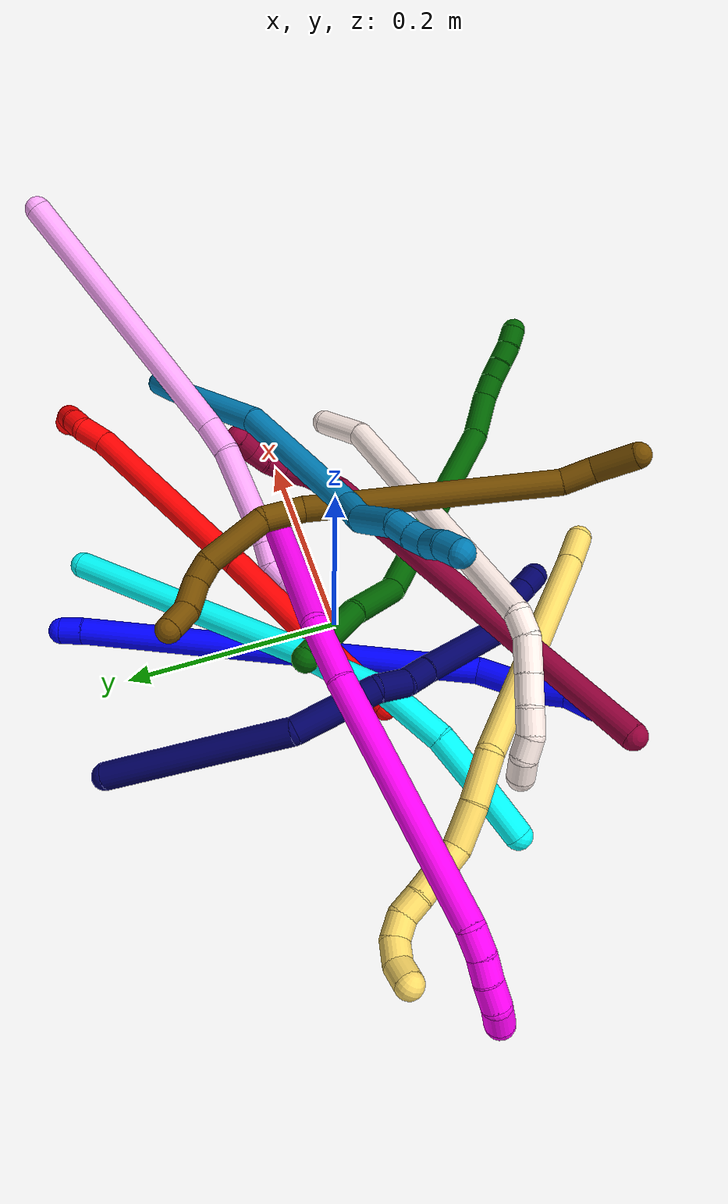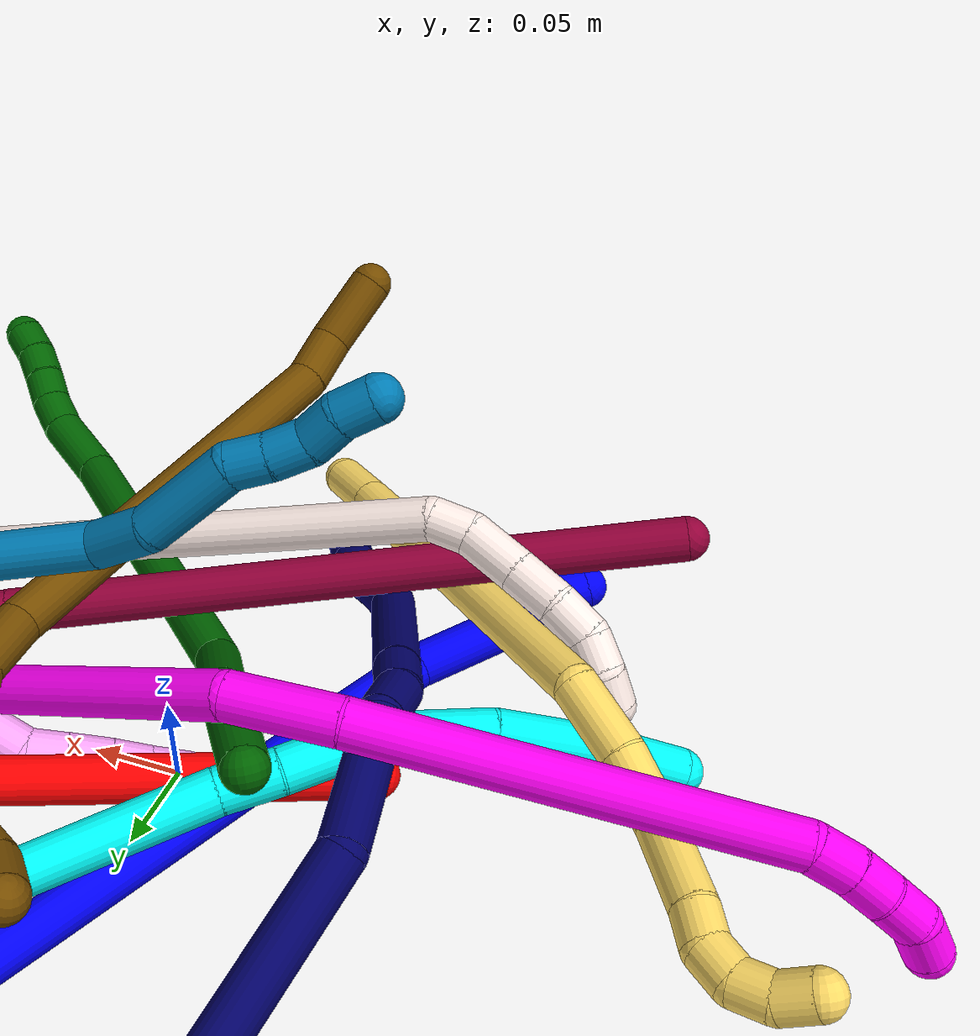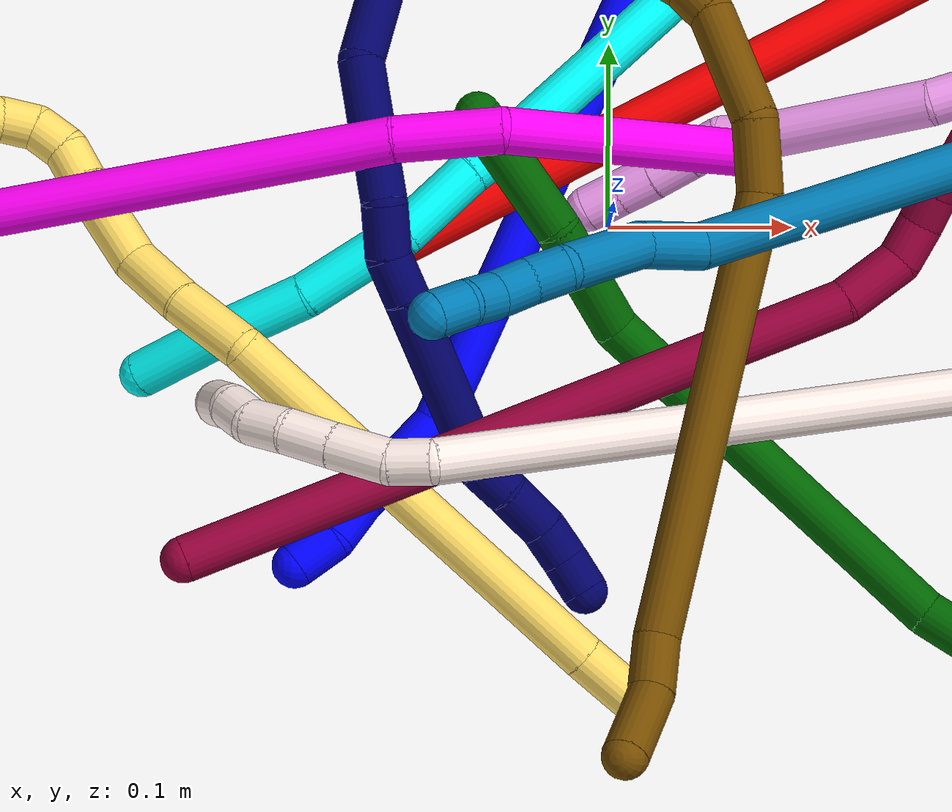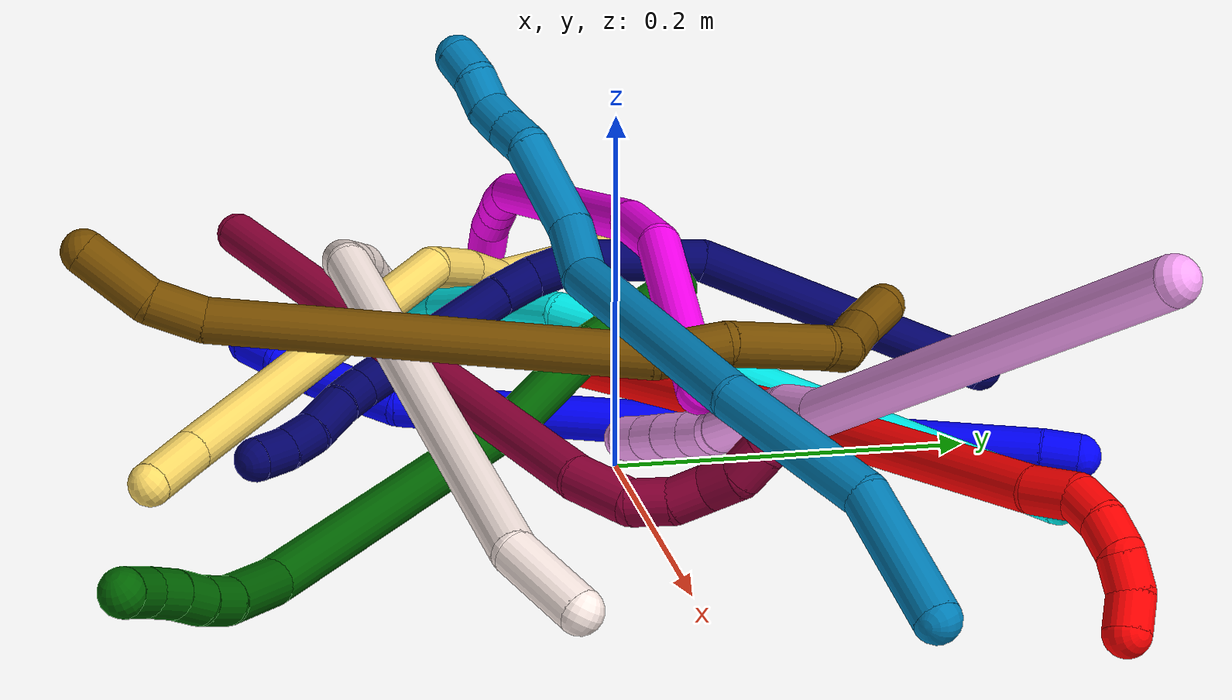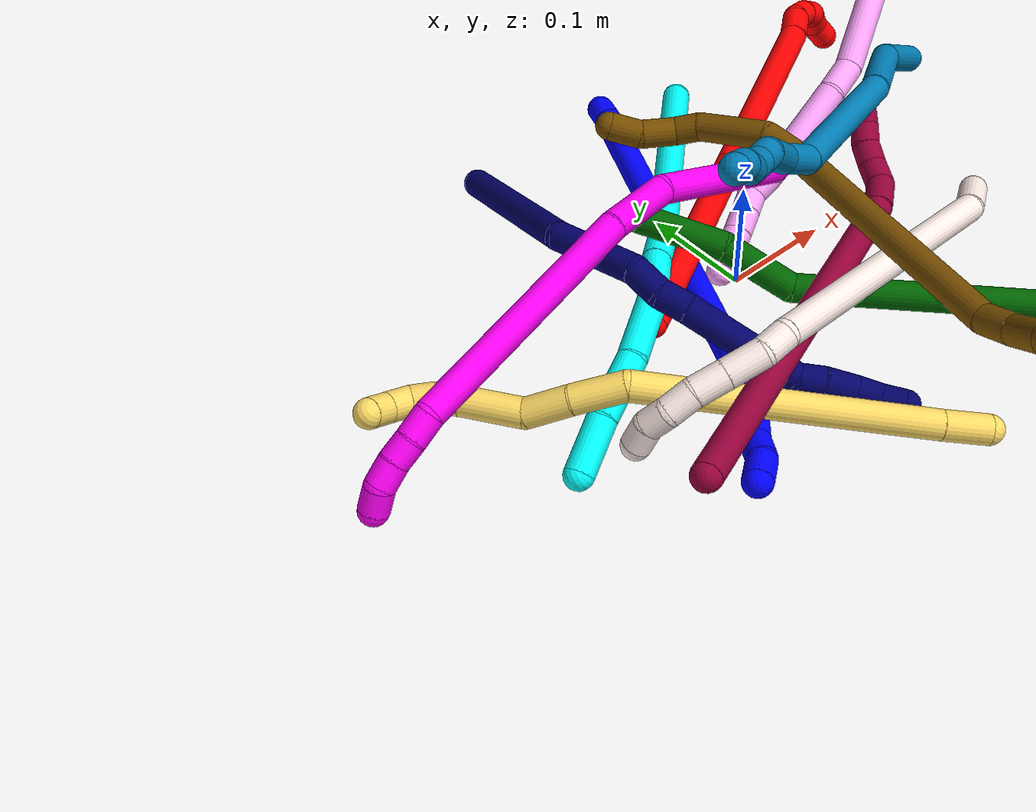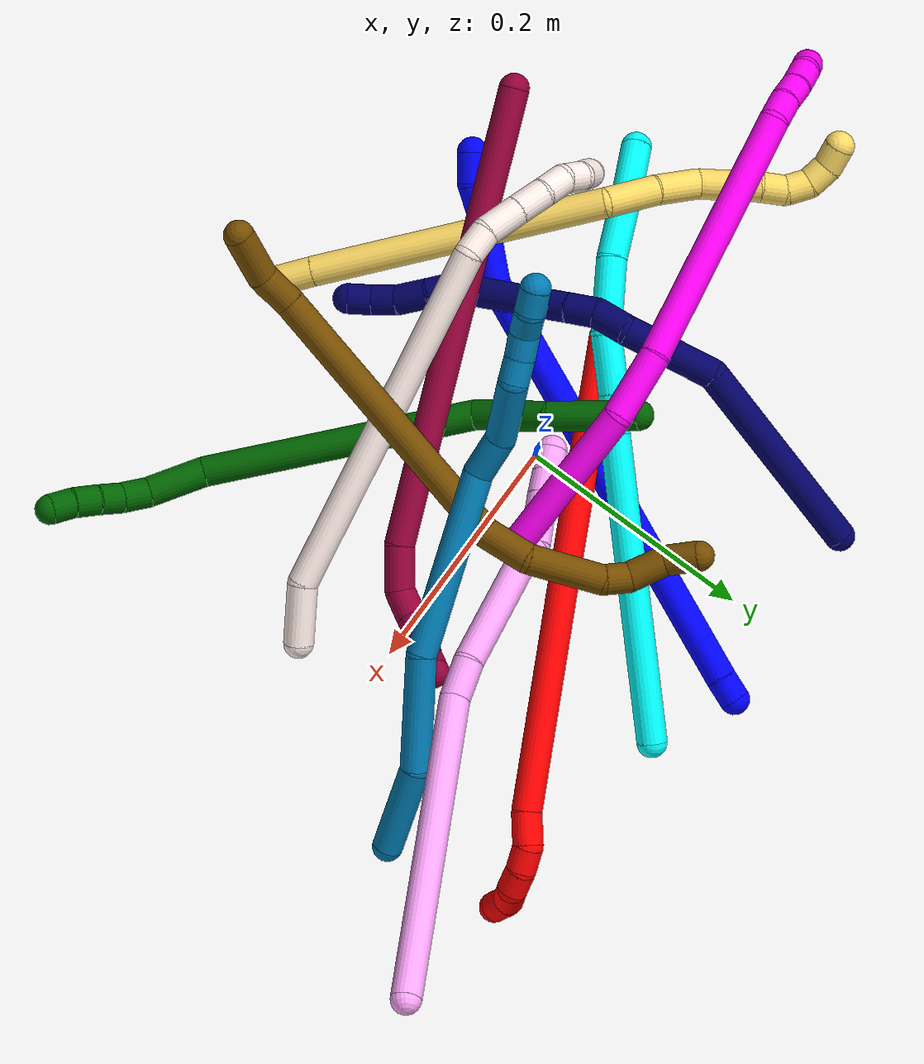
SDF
<sdf version="1.7">
 <world name="default">
  <plugin name="TubeGeneratorPlugin" filename="libtube_generator_plugin.so"/>
  <model name="photoneo_s_sensor">
   <static>1</static>
   <pose>0 0 2 1.57079 1.57079 3.14159</pose>
   <link name="link">
    <inertial><mass>0.1</mass></inertial>
    <sensor name="sensor" type="depth">
     <update_rate>30</update_rate>
     <camera>
      <horizontal_fov>1.22</horizontal_fov>
      <image><width>1920</width><height>1200</height><format>B8G8R8</format></image>
      <clip><near>0.1</near><far>4</far></clip>
      <depth_camera><output>points</output></depth_camera>
     </camera>
     <plugin name="camera_plugin" filename="libgazebo_ros_depth_camera.so">
      <baseline>0.2</baseline>
      <alwaysOn>1</alwaysOn>
      <updateRate>0.0</updateRate>
      <cameraName>camera_ir</cameraName>
      <imageTopicName>/camera/color/image_raw</imageTopicName>
      <cameraInfoTopicName>/camera/color/camera_info</cameraInfoTopicName>
      <depthImageTopicName>/camera/depth/image_raw</depthImageTopicName>
      <depthImageCameraInfoTopicName>/camera/depth/camera_info</depthImageCameraInfoTopicName>
      <pointCloudTopicName>/camera/depth/points</pointCloudTopicName>
      <frameName>fr_optical</frameName>
      <pointCloudCutoff>0.1</pointCloudCutoff>
      <pointCloudCutoffMax>2.0</pointCloudCutoffMax>
      <distortionK1>0</distortionK1>
      <distortionK2>0</distortionK2>
      <distortionK3>0</distortionK3>
      <distortionT1>0</distortionT1>
      <distortionT2>0</distortionT2>
      <CxPrime>0</CxPrime>
      <Cx>0</Cx>
      <Cy>0</Cy>
      <focalLength>0</focalLength>
      <hackBaseline>0</hackBaseline>
     </plugin>
    </sensor>
   </link>
  </model>
  <gravity>0 0 -9.8</gravity>
  <magnetic_field>6e-06 2.3e-05 -4.2e-05</magnetic_field>
  <atmosphere type="adiabatic"/>
  <physics name="default_physics" default="0" type="ode">
   <max_step_size>0.003</max_step_size>
   <real_time_factor>1</real_time_factor>
   <real_time_update_rate>1000</real_time_update_rate>
   <max_contacts>10000</max_contacts>
   <ode>
    <solver>
     <type>quick</type>
     <iters>100</iters>
     <sor>1.3</sor>
     <use_dynamic_moi_rescaling>0</use_dynamic_moi_rescaling>
    </solver>
    <constraints>
     <contact_max_correcting_vel>0</contact_max_correcting_vel>
     <contact_surface_layer>0.001</contact_surface_layer>
     <cfm>0</cfm>
     <erp>0.2</erp>
    </constraints>
   </ode>
  </physics>
  <scene><ambient>0.4 0.4 0.4 1</ambient><background>0.7 0.7 0.7 1</background><shadows>0</shadows></scene>
  <audio><device>default</device></audio>
  <spherical_coordinates>
   <surface_model>EARTH_WGS84</surface_model>
   <latitude_deg>0</latitude_deg>
   <longitude_deg>0</longitude_deg>
   <elevation>0</elevation>
   <heading_deg>0</heading_deg>
  </spherical_coordinates>
  <model name="bin">
   <static>1</static>
   <link name="bottom">
    <collision name="collision-bottom">
     <pose>0 0 -0.01 0 -0 0</pose>
     <geometry><box><size>0.8 0.6 0.02</size></box></geometry>
     <surface>
      <friction><ode><mu>100</mu><mu2>100</mu2></ode></friction>
      <contact><collide_bitmask>65535</collide_bitmask></contact>
     </surface>
    </collision>
   </link>
   <link name="west_wall">
    <collision name="collision-west_wall">
     <pose>-0.41 0 0.1 0 -0 0</pose>
     <geometry><box><size>0.02 0.6 0.2</size></box></geometry>
     <surface>
      <friction><ode><mu>100</mu><mu2>100</mu2></ode></friction>
      <contact><collide_bitmask>65535</collide_bitmask></contact>
     </surface>
    </collision>
   </link>
   <link name="east_wall">
    <collision name="collision-east_wall">
     <pose>0.41 0 0.1 0 -0 0</pose>
     <geometry><box><size>0.02 0.6 0.2</size></box></geometry>
     <surface>
      <friction><ode><mu>100</mu><mu2>100</mu2></ode></friction>
      <contact><collide_bitmask>65535</collide_bitmask></contact>
     </surface>
    </collision>
   </link>
   <link name="south_wall">
    <collision name="collision-south_wall">
     <pose>0 -0.31 0.1 0 -0 0</pose>
     <geometry><box><size>0.8 0.02 0.2</size></box></geometry>
     <surface>
      <friction><ode><mu>100</mu><mu2>100</mu2></ode></friction>
      <contact><collide_bitmask>65535</collide_bitmask></contact>
     </surface>
    </collision>
   </link>
   <link name="north_wall">
    <collision name="collision-north_wall">
     <pose>0 0.31 0.1 0 -0 0</pose>
     <geometry><box><size>0.8 0.02 0.2</size></box></geometry>
     <surface>
      <friction><ode><mu>100</mu><mu2>100</mu2></ode></friction>
      <contact><collide_bitmask>65535</collide_bitmask></contact>
     </surface>
    </collision>
   </link>
  </model>
  <model name="1">
   <static>0</static>
   <link name="1">
    <collision name="collision-cylinder-e_1_1_4">
     <pose>-0.003154 -0.008823 0.004397 1.10851 -0.309624 -0.192598</pose>
     <geometry><cylinder><radius>0.0125</radius><length>0.0207</length></cylinder></geometry>
     <surface>
      <friction><ode><mu>1.16</mu><mu2>1.16</mu2><slip1>0</slip1><slip2>0</slip2></ode></friction>
      <contact><ode><kp>1e+06</kp><kd>1</kd><max_vel>0</max_vel><min_depth>0.001</min_depth></ode></contact>
     </surface>
    </collision>
    <visual name="visual-cylinder-e_1_1_4">
     <pose>-0.003154 -0.008823 0.004397 1.10851 -0.309624 -0.192598</pose>
     <geometry><cylinder><radius>0.0125</radius><length>0.0207</length></cylinder></geometry>
     <material><ambient>0 0 1 1</ambient></material>
    </visual>
    <collision name="collision-cylinder-e_2_4_5">
     <pose>-0.07992 -0.168412 0.085722 1.09898 -0.410235 -0.253447</pose>
     <geometry><cylinder><radius>0.0125</radius><length>0.369146</length></cylinder></geometry>
     <surface>
      <friction><ode><mu>1.16</mu><mu2>1.16</mu2><slip1>0</slip1><slip2>0</slip2></ode></friction>
      <contact><ode><kp>1e+06</kp><kd>1</kd><max_vel>0</max_vel><min_depth>0.001</min_depth></ode></contact>
     </surface>
    </collision>
    <visual name="visual-cylinder-e_2_4_5">
     <pose>-0.07992 -0.168412 0.085722 1.09898 -0.410235 -0.253447</pose>
     <geometry><cylinder><radius>0.0125</radius><length>0.369146</length></cylinder></geometry>
     <material><ambient>0 0 1 1</ambient></material>
    </visual>
    <collision name="collision-cylinder-e_3_5_6">
     <pose>-0.164444 -0.336703 0.183015 0.710622 -0.385794 -0.144702</pose>
     <geometry><cylinder><radius>0.0125</radius><length>0.057996</length></cylinder></geometry>
     <surface>
      <friction><ode><mu>1.16</mu><mu2>1.16</mu2><slip1>0</slip1><slip2>0</slip2></ode></friction>
      <contact><ode><kp>1e+06</kp><kd>1</kd><max_vel>0</max_vel><min_depth>0.001</min_depth></ode></contact>
     </surface>
    </collision>
    <visual name="visual-cylinder-e_3_5_6">
     <pose>-0.164444 -0.336703 0.183015 0.710622 -0.385794 -0.144702</pose>
     <geometry><cylinder><radius>0.0125</radius><length>0.057996</length></cylinder></geometry>
     <material><ambient>0 0 1 1</ambient></material>
    </visual>
    <collision name="collision-cylinder-e_4_6_7">
     <pose>-0.177778 -0.363708 0.212545 0.802185 -0.181674 -0.077219</pose>
     <geometry><cylinder><radius>0.0125</radius><length>0.026814</length></cylinder></geometry>
     <surface>
      <friction><ode><mu>1.16</mu><mu2>1.16</mu2><slip1>0</slip1><slip2>0</slip2></ode></friction>
      <contact><ode><kp>1e+06</kp><kd>1</kd><max_vel>0</max_vel><min_depth>0.001</min_depth></ode></contact>
     </surface>
    </collision>
    <visual name="visual-cylinder-e_4_6_7">
     <pose>-0.177778 -0.363708 0.212545 0.802185 -0.181674 -0.077219</pose>
     <geometry><cylinder><radius>0.0125</radius><length>0.026814</length></cylinder></geometry>
     <material><ambient>0 0 1 1</ambient></material>
    </visual>
    <collision name="collision-cylinder-e_5_7_2">
     <pose>-0.18513 -0.378946 0.231866 0.515874 -0.399573 -0.106737</pose>
     <geometry><cylinder><radius>0.0125</radius><length>0.025344</length></cylinder></geometry>
     <surface>
      <friction><ode><mu>1.16</mu><mu2>1.16</mu2><slip1>0</slip1><slip2>0</slip2></ode></friction>
      <contact><ode><kp>1e+06</kp><kd>1</kd><max_vel>0</max_vel><min_depth>0.001</min_depth></ode></contact>
     </surface>
    </collision>
    <visual name="visual-cylinder-e_5_7_2">
     <pose>-0.18513 -0.378946 0.231866 0.515874 -0.399573 -0.106737</pose>
     <geometry><cylinder><radius>0.0125</radius><length>0.025344</length></cylinder></geometry>
     <material><ambient>0 0 1 1</ambient></material>
    </visual>
    <collision name="collision-sphere-2">
     <pose>-0.19006 -0.384704 0.242021 0 -0 0</pose>
     <geometry><sphere><radius>0.0125</radius></sphere></geometry>
     <surface>
      <friction><ode><mu>1.16</mu><mu2>1.16</mu2><slip1>0</slip1><slip2>0</slip2></ode></friction>
      <contact><ode><kp>1e+06</kp><kd>1</kd><max_vel>0</max_vel><min_depth>0.001</min_depth></ode></contact>
     </surface>
    </collision>
    <visual name="visual-sphere-2">
     <pose>-0.19006 -0.384704 0.242021 0 -0 0</pose>
     <geometry><sphere><radius>0.0125</radius></sphere></geometry>
     <material><ambient>0 0 1 1</ambient></material>
    </visual>
    <collision name="collision-sphere-7">
     <pose>-0.1802 -0.373187 0.221712 0 -0 0</pose>
     <geometry><sphere><radius>0.0125</radius></sphere></geometry>
     <surface>
      <friction><ode><mu>1.16</mu><mu2>1.16</mu2><slip1>0</slip1><slip2>0</slip2></ode></friction>
      <contact><ode><kp>1e+06</kp><kd>1</kd><max_vel>0</max_vel><min_depth>0.001</min_depth></ode></contact>
     </surface>
    </collision>
    <visual name="visual-sphere-7">
     <pose>-0.1802 -0.373187 0.221712 0 -0 0</pose>
     <geometry><sphere><radius>0.0125</radius></sphere></geometry>
     <material><ambient>0 0 1 1</ambient></material>
    </visual>
    <collision name="collision-sphere-6">
     <pose>-0.175356 -0.354228 0.203379 0 -0 0</pose>
     <geometry><sphere><radius>0.0125</radius></sphere></geometry>
     <surface>
      <friction><ode><mu>1.16</mu><mu2>1.16</mu2><slip1>0</slip1><slip2>0</slip2></ode></friction>
      <contact><ode><kp>1e+06</kp><kd>1</kd><max_vel>0</max_vel><min_depth>0.001</min_depth></ode></contact>
     </surface>
    </collision>
    <visual name="visual-sphere-6">
     <pose>-0.175356 -0.354228 0.203379 0 -0 0</pose>
     <geometry><sphere><radius>0.0125</radius></sphere></geometry>
     <material><ambient>0 0 1 1</ambient></material>
    </visual>
    <collision name="collision-sphere-5">
     <pose>-0.153532 -0.319178 0.162652 0 -0 0</pose>
     <geometry><sphere><radius>0.0125</radius></sphere></geometry>
     <surface>
      <friction><ode><mu>1.16</mu><mu2>1.16</mu2><slip1>0</slip1><slip2>0</slip2></ode></friction>
      <contact><ode><kp>1e+06</kp><kd>1</kd><max_vel>0</max_vel><min_depth>0.001</min_depth></ode></contact>
     </surface>
    </collision>
    <visual name="visual-sphere-5">
     <pose>-0.153532 -0.319178 0.162652 0 -0 0</pose>
     <geometry><sphere><radius>0.0125</radius></sphere></geometry>
     <material><ambient>0 0 1 1</ambient></material>
    </visual>
    <collision name="collision-sphere-1">
     <geometry><sphere><radius>0.0125</radius></sphere></geometry>
     <surface>
      <friction><ode><mu>1.16</mu><mu2>1.16</mu2><slip1>0</slip1><slip2>0</slip2></ode></friction>
      <contact><ode><kp>1e+06</kp><kd>1</kd><max_vel>0</max_vel><min_depth>0.001</min_depth></ode></contact>
     </surface>
    </collision>
    <visual name="visual-sphere-1">
     <geometry><sphere><radius>0.0125</radius></sphere></geometry>
     <material><ambient>0 0 1 1</ambient></material>
    </visual>
    <collision name="collision-sphere-4">
     <pose>-0.006307 -0.017646 0.008793 0 -0 0</pose>
     <geometry><sphere><radius>0.0125</radius></sphere></geometry>
     <surface>
      <friction><ode><mu>1.16</mu><mu2>1.16</mu2><slip1>0</slip1><slip2>0</slip2></ode></friction>
      <contact><ode><kp>1e+06</kp><kd>1</kd><max_vel>0</max_vel><min_depth>0.001</min_depth></ode></contact>
     </surface>
    </collision>
    <visual name="visual-sphere-4">
     <pose>-0.006307 -0.017646 0.008793 0 -0 0</pose>
     <geometry><sphere><radius>0.0125</radius></sphere></geometry>
     <material><ambient>0 0 1 1</ambient></material>
    </visual>
    <inertial>
     <pose>-0.097127 -0.20247 0.10785 0 -0 0</pose>
     <mass>0.5</mass>
     <inertia>
      <ixx>0.002772</ixx>
      <ixy>0</ixy>
      <ixz>0</ixz>
      <iyy>0.001244</iyy>
      <iyz>0</iyz>
      <izz>0.005157</izz>
     </inertia>
    </inertial>
   </link>
   <pose>0.064402 0.247692 0.011495 -0.297336 -1.01832 0.432797</pose>
  </model>
  <model name="2">
   <static>0</static>
   <link name="2">
    <collision name="collision-cylinder-e_1_1_4">
     <pose>0.022266 0.009698 0.095081 -0.101648 0.228883 -0.011694</pose>
     <geometry><cylinder><radius>0.0125</radius><length>0.196268</length></cylinder></geometry>
     <surface>
      <friction><ode><mu>1.16</mu><mu2>1.16</mu2><slip1>0</slip1><slip2>0</slip2></ode></friction>
      <contact><ode><kp>1e+06</kp><kd>1</kd><max_vel>0</max_vel><min_depth>0.001</min_depth></ode></contact>
     </surface>
    </collision>
    <visual name="visual-cylinder-e_1_1_4">
     <pose>0.022266 0.009698 0.095081 -0.101648 0.228883 -0.011694</pose>
     <geometry><cylinder><radius>0.0125</radius><length>0.196268</length></cylinder></geometry>
     <material><ambient>1 0 0 1</ambient></material>
    </visual>
    <collision name="collision-cylinder-e_2_4_5">
     <pose>0.069897 0.030941 0.283435 -0.12314 0.263616 -0.016346</pose>
     <geometry><cylinder><radius>0.0125</radius><length>0.194695</length></cylinder></geometry>
     <surface>
      <friction><ode><mu>1.16</mu><mu2>1.16</mu2><slip1>0</slip1><slip2>0</slip2></ode></friction>
      <contact><ode><kp>1e+06</kp><kd>1</kd><max_vel>0</max_vel><min_depth>0.001</min_depth></ode></contact>
     </surface>
    </collision>
    <visual name="visual-cylinder-e_2_4_5">
     <pose>0.069897 0.030941 0.283435 -0.12314 0.263616 -0.016346</pose>
     <geometry><cylinder><radius>0.0125</radius><length>0.194695</length></cylinder></geometry>
     <material><ambient>1 0 0 1</ambient></material>
    </visual>
    <collision name="collision-cylinder-e_3_5_6">
     <pose>0.097374 0.046473 0.389643 -0.299104 0.154718 -0.023358</pose>
     <geometry><cylinder><radius>0.0125</radius><length>0.027398</length></cylinder></geometry>
     <surface>
      <friction><ode><mu>1.16</mu><mu2>1.16</mu2><slip1>0</slip1><slip2>0</slip2></ode></friction>
      <contact><ode><kp>1e+06</kp><kd>1</kd><max_vel>0</max_vel><min_depth>0.001</min_depth></ode></contact>
     </surface>
    </collision>
    <visual name="visual-cylinder-e_3_5_6">
     <pose>0.097374 0.046473 0.389643 -0.299104 0.154718 -0.023358</pose>
     <geometry><cylinder><radius>0.0125</radius><length>0.027398</length></cylinder></geometry>
     <material><ambient>1 0 0 1</ambient></material>
    </visual>
    <collision name="collision-cylinder-e_4_6_7">
     <pose>0.105711 0.051683 0.410718 -0.148908 0.647503 -0.050049</pose>
     <geometry><cylinder><radius>0.0125</radius><length>0.020641</length></cylinder></geometry>
     <surface>
      <friction><ode><mu>1.16</mu><mu2>1.16</mu2><slip1>0</slip1><slip2>0</slip2></ode></friction>
      <contact><ode><kp>1e+06</kp><kd>1</kd><max_vel>0</max_vel><min_depth>0.001</min_depth></ode></contact>
     </surface>
    </collision>
    <visual name="visual-cylinder-e_4_6_7">
     <pose>0.105711 0.051683 0.410718 -0.148908 0.647503 -0.050049</pose>
     <geometry><cylinder><radius>0.0125</radius><length>0.020641</length></cylinder></geometry>
     <material><ambient>1 0 0 1</ambient></material>
    </visual>
    <collision name="collision-cylinder-e_5_7_8">
     <pose>0.120106 0.053817 0.425001 -0.147547 0.92079 -0.073275</pose>
     <geometry><cylinder><radius>0.0125</radius><length>0.020525</length></cylinder></geometry>
     <surface>
      <friction><ode><mu>1.16</mu><mu2>1.16</mu2><slip1>0</slip1><slip2>0</slip2></ode></friction>
      <contact><ode><kp>1e+06</kp><kd>1</kd><max_vel>0</max_vel><min_depth>0.001</min_depth></ode></contact>
     </surface>
    </collision>
    <visual name="visual-cylinder-e_5_7_8">
     <pose>0.120106 0.053817 0.425001 -0.147547 0.92079 -0.073275</pose>
     <geometry><cylinder><radius>0.0125</radius><length>0.020525</length></cylinder></geometry>
     <material><ambient>1 0 0 1</ambient></material>
    </visual>
    <collision name="collision-cylinder-e_6_8_9">
     <pose>0.137885 0.057685 0.432807 -1.05823 1.23155 -0.784567</pose>
     <geometry><cylinder><radius>0.0125</radius><length>0.02038</length></cylinder></geometry>
     <surface>
      <friction><ode><mu>1.16</mu><mu2>1.16</mu2><slip1>0</slip1><slip2>0</slip2></ode></friction>
      <contact><ode><kp>1e+06</kp><kd>1</kd><max_vel>0</max_vel><min_depth>0.001</min_depth></ode></contact>
     </surface>
    </collision>
    <visual name="visual-cylinder-e_6_8_9">
     <pose>0.137885 0.057685 0.432807 -1.05823 1.23155 -0.784567</pose>
     <geometry><cylinder><radius>0.0125</radius><length>0.02038</length></cylinder></geometry>
     <material><ambient>1 0 0 1</ambient></material>
    </visual>
    <collision name="collision-cylinder-e_7_9_2">
     <pose>0.1574 0.059241 0.435386 0.991473 1.40359 0.857575</pose>
     <geometry><cylinder><radius>0.0125</radius><length>0.020094</length></cylinder></geometry>
     <surface>
      <friction><ode><mu>1.16</mu><mu2>1.16</mu2><slip1>0</slip1><slip2>0</slip2></ode></friction>
      <contact><ode><kp>1e+06</kp><kd>1</kd><max_vel>0</max_vel><min_depth>0.001</min_depth></ode></contact>
     </surface>
    </collision>
    <visual name="visual-cylinder-e_7_9_2">
     <pose>0.1574 0.059241 0.435386 0.991473 1.40359 0.857575</pose>
     <geometry><cylinder><radius>0.0125</radius><length>0.020094</length></cylinder></geometry>
     <material><ambient>1 0 0 1</ambient></material>
    </visual>
    <collision name="collision-sphere-2">
     <pose>0.167307 0.057842 0.436301 0 -0 0</pose>
     <geometry><sphere><radius>0.0125</radius></sphere></geometry>
     <surface>
      <friction><ode><mu>1.16</mu><mu2>1.16</mu2><slip1>0</slip1><slip2>0</slip2></ode></friction>
      <contact><ode><kp>1e+06</kp><kd>1</kd><max_vel>0</max_vel><min_depth>0.001</min_depth></ode></contact>
     </surface>
    </collision>
    <visual name="visual-sphere-2">
     <pose>0.167307 0.057842 0.436301 0 -0 0</pose>
     <geometry><sphere><radius>0.0125</radius></sphere></geometry>
     <material><ambient>1 0 0 1</ambient></material>
    </visual>
    <collision name="collision-sphere-9">
     <pose>0.147494 0.06064 0.43447 0 -0 0</pose>
     <geometry><sphere><radius>0.0125</radius></sphere></geometry>
     <surface>
      <friction><ode><mu>1.16</mu><mu2>1.16</mu2><slip1>0</slip1><slip2>0</slip2></ode></friction>
      <contact><ode><kp>1e+06</kp><kd>1</kd><max_vel>0</max_vel><min_depth>0.001</min_depth></ode></contact>
     </surface>
    </collision>
    <visual name="visual-sphere-9">
     <pose>0.147494 0.06064 0.43447 0 -0 0</pose>
     <geometry><sphere><radius>0.0125</radius></sphere></geometry>
     <material><ambient>1 0 0 1</ambient></material>
    </visual>
    <collision name="collision-sphere-4">
     <pose>0.044531 0.019397 0.190162 0 -0 0</pose>
     <geometry><sphere><radius>0.0125</radius></sphere></geometry>
     <surface>
      <friction><ode><mu>1.16</mu><mu2>1.16</mu2><slip1>0</slip1><slip2>0</slip2></ode></friction>
      <contact><ode><kp>1e+06</kp><kd>1</kd><max_vel>0</max_vel><min_depth>0.001</min_depth></ode></contact>
     </surface>
    </collision>
    <visual name="visual-sphere-4">
     <pose>0.044531 0.019397 0.190162 0 -0 0</pose>
     <geometry><sphere><radius>0.0125</radius></sphere></geometry>
     <material><ambient>1 0 0 1</ambient></material>
    </visual>
    <collision name="collision-sphere-1">
     <geometry><sphere><radius>0.0125</radius></sphere></geometry>
     <surface>
      <friction><ode><mu>1.16</mu><mu2>1.16</mu2><slip1>0</slip1><slip2>0</slip2></ode></friction>
      <contact><ode><kp>1e+06</kp><kd>1</kd><max_vel>0</max_vel><min_depth>0.001</min_depth></ode></contact>
     </surface>
    </collision>
    <visual name="visual-sphere-1">
     <geometry><sphere><radius>0.0125</radius></sphere></geometry>
     <material><ambient>1 0 0 1</ambient></material>
    </visual>
    <collision name="collision-sphere-8">
     <pose>0.128276 0.05473 0.431145 0 -0 0</pose>
     <geometry><sphere><radius>0.0125</radius></sphere></geometry>
     <surface>
      <friction><ode><mu>1.16</mu><mu2>1.16</mu2><slip1>0</slip1><slip2>0</slip2></ode></friction>
      <contact><ode><kp>1e+06</kp><kd>1</kd><max_vel>0</max_vel><min_depth>0.001</min_depth></ode></contact>
     </surface>
    </collision>
    <visual name="visual-sphere-8">
     <pose>0.128276 0.05473 0.431145 0 -0 0</pose>
     <geometry><sphere><radius>0.0125</radius></sphere></geometry>
     <material><ambient>1 0 0 1</ambient></material>
    </visual>
    <collision name="collision-sphere-5">
     <pose>0.095263 0.042485 0.376708 0 -0 0</pose>
     <geometry><sphere><radius>0.0125</radius></sphere></geometry>
     <surface>
      <friction><ode><mu>1.16</mu><mu2>1.16</mu2><slip1>0</slip1><slip2>0</slip2></ode></friction>
      <contact><ode><kp>1e+06</kp><kd>1</kd><max_vel>0</max_vel><min_depth>0.001</min_depth></ode></contact>
     </surface>
    </collision>
    <visual name="visual-sphere-5">
     <pose>0.095263 0.042485 0.376708 0 -0 0</pose>
     <geometry><sphere><radius>0.0125</radius></sphere></geometry>
     <material><ambient>1 0 0 1</ambient></material>
    </visual>
    <collision name="collision-sphere-6">
     <pose>0.099486 0.050462 0.402577 0 -0 0</pose>
     <geometry><sphere><radius>0.0125</radius></sphere></geometry>
     <surface>
      <friction><ode><mu>1.16</mu><mu2>1.16</mu2><slip1>0</slip1><slip2>0</slip2></ode></friction>
      <contact><ode><kp>1e+06</kp><kd>1</kd><max_vel>0</max_vel><min_depth>0.001</min_depth></ode></contact>
     </surface>
    </collision>
    <visual name="visual-sphere-6">
     <pose>0.099486 0.050462 0.402577 0 -0 0</pose>
     <geometry><sphere><radius>0.0125</radius></sphere></geometry>
     <material><ambient>1 0 0 1</ambient></material>
    </visual>
    <collision name="collision-sphere-7">
     <pose>0.111936 0.052904 0.418858 0 -0 0</pose>
     <geometry><sphere><radius>0.0125</radius></sphere></geometry>
     <surface>
      <friction><ode><mu>1.16</mu><mu2>1.16</mu2><slip1>0</slip1><slip2>0</slip2></ode></friction>
      <contact><ode><kp>1e+06</kp><kd>1</kd><max_vel>0</max_vel><min_depth>0.001</min_depth></ode></contact>
     </surface>
    </collision>
    <visual name="visual-sphere-7">
     <pose>0.111936 0.052904 0.418858 0 -0 0</pose>
     <geometry><sphere><radius>0.0125</radius></sphere></geometry>
     <material><ambient>1 0 0 1</ambient></material>
    </visual>
    <inertial>
     <pose>0.062533 0.027476 0.23858 0 -0 0</pose>
     <mass>0.5</mass>
     <inertia>
      <ixx>0.001223</ixx>
      <ixy>0</ixy>
      <ixz>0</ixz>
      <iyy>0.001248</iyy>
      <iyz>0</iyz>
      <izz>-0.000416</izz>
     </inertia>
    </inertial>
   </link>
   <pose>-0.110003 -0.011605 0.027673 -0.76998 1.07147 -0.381204</pose>
  </model>
  <model name="3">
   <static>0</static>
   <link name="3">
    <collision name="collision-cylinder-e_1_1_4">
     <pose>-0.047762 -0.117275 0.005535 1.52363 -0.386363 -0.368968</pose>
     <geometry><cylinder><radius>0.0125</radius><length>0.253499</length></cylinder></geometry>
     <surface>
      <friction><ode><mu>1.16</mu><mu2>1.16</mu2><slip1>0</slip1><slip2>0</slip2></ode></friction>
      <contact><ode><kp>1e+06</kp><kd>1</kd><max_vel>0</max_vel><min_depth>0.001</min_depth></ode></contact>
     </surface>
    </collision>
    <visual name="visual-cylinder-e_1_1_4">
     <pose>-0.047762 -0.117275 0.005535 1.52363 -0.386363 -0.368968</pose>
     <geometry><cylinder><radius>0.0125</radius><length>0.253499</length></cylinder></geometry>
     <material><ambient>0.003922 1 0.996078 1</ambient></material>
    </visual>
    <collision name="collision-cylinder-e_2_4_5">
     <pose>-0.100873 -0.249283 0.013206 1.42684 -0.344972 -0.299314</pose>
     <geometry><cylinder><radius>0.0125</radius><length>0.031637</length></cylinder></geometry>
     <surface>
      <friction><ode><mu>1.16</mu><mu2>1.16</mu2><slip1>0</slip1><slip2>0</slip2></ode></friction>
      <contact><ode><kp>1e+06</kp><kd>1</kd><max_vel>0</max_vel><min_depth>0.001</min_depth></ode></contact>
     </surface>
    </collision>
    <visual name="visual-cylinder-e_2_4_5">
     <pose>-0.100873 -0.249283 0.013206 1.42684 -0.344972 -0.299314</pose>
     <geometry><cylinder><radius>0.0125</radius><length>0.031637</length></cylinder></geometry>
     <material><ambient>0.003922 1 0.996078 1</ambient></material>
    </visual>
    <collision name="collision-cylinder-e_3_5_6">
     <pose>-0.116837 -0.286062 0.017229 1.48538 -0.447291 -0.4117</pose>
     <geometry><cylinder><radius>0.0125</radius><length>0.049083</length></cylinder></geometry>
     <surface>
      <friction><ode><mu>1.16</mu><mu2>1.16</mu2><slip1>0</slip1><slip2>0</slip2></ode></friction>
      <contact><ode><kp>1e+06</kp><kd>1</kd><max_vel>0</max_vel><min_depth>0.001</min_depth></ode></contact>
     </surface>
    </collision>
    <visual name="visual-cylinder-e_3_5_6">
     <pose>-0.116837 -0.286062 0.017229 1.48538 -0.447291 -0.4117</pose>
     <geometry><cylinder><radius>0.0125</radius><length>0.049083</length></cylinder></geometry>
     <material><ambient>0.003922 1 0.996078 1</ambient></material>
    </visual>
    <collision name="collision-cylinder-e_4_6_7">
     <pose>-0.141863 -0.333016 0.030416 1.14489 -0.484948 -0.316126</pose>
     <geometry><cylinder><radius>0.0125</radius><length>0.061829</length></cylinder></geometry>
     <surface>
      <friction><ode><mu>1.16</mu><mu2>1.16</mu2><slip1>0</slip1><slip2>0</slip2></ode></friction>
      <contact><ode><kp>1e+06</kp><kd>1</kd><max_vel>0</max_vel><min_depth>0.001</min_depth></ode></contact>
     </surface>
    </collision>
    <visual name="visual-cylinder-e_4_6_7">
     <pose>-0.141863 -0.333016 0.030416 1.14489 -0.484948 -0.316126</pose>
     <geometry><cylinder><radius>0.0125</radius><length>0.061829</length></cylinder></geometry>
     <material><ambient>0.003922 1 0.996078 1</ambient></material>
    </visual>
    <collision name="collision-cylinder-e_5_7_8">
     <pose>-0.168846 -0.378027 0.056852 0.925435 -0.463289 -0.234253</pose>
     <geometry><cylinder><radius>0.0125</radius><length>0.056262</length></cylinder></geometry>
     <surface>
      <friction><ode><mu>1.16</mu><mu2>1.16</mu2><slip1>0</slip1><slip2>0</slip2></ode></friction>
      <contact><ode><kp>1e+06</kp><kd>1</kd><max_vel>0</max_vel><min_depth>0.001</min_depth></ode></contact>
     </surface>
    </collision>
    <visual name="visual-cylinder-e_5_7_8">
     <pose>-0.168846 -0.378027 0.056852 0.925435 -0.463289 -0.234253</pose>
     <geometry><cylinder><radius>0.0125</radius><length>0.056262</length></cylinder></geometry>
     <material><ambient>0.003922 1 0.996078 1</ambient></material>
    </visual>
    <collision name="collision-cylinder-e_6_8_2">
     <pose>-0.19454 -0.412566 0.085702 0.811017 -0.582737 -0.25609</pose>
     <geometry><cylinder><radius>0.0125</radius><length>0.04769</length></cylinder></geometry>
     <surface>
      <friction><ode><mu>1.16</mu><mu2>1.16</mu2><slip1>0</slip1><slip2>0</slip2></ode></friction>
      <contact><ode><kp>1e+06</kp><kd>1</kd><max_vel>0</max_vel><min_depth>0.001</min_depth></ode></contact>
     </surface>
    </collision>
    <visual name="visual-cylinder-e_6_8_2">
     <pose>-0.19454 -0.412566 0.085702 0.811017 -0.582737 -0.25609</pose>
     <geometry><cylinder><radius>0.0125</radius><length>0.04769</length></cylinder></geometry>
     <material><ambient>0.003922 1 0.996078 1</ambient></material>
    </visual>
    <collision name="collision-sphere-2">
     <pose>-0.207662 -0.427 0.099415 0 -0 0</pose>
     <geometry><sphere><radius>0.0125</radius></sphere></geometry>
     <surface>
      <friction><ode><mu>1.16</mu><mu2>1.16</mu2><slip1>0</slip1><slip2>0</slip2></ode></friction>
      <contact><ode><kp>1e+06</kp><kd>1</kd><max_vel>0</max_vel><min_depth>0.001</min_depth></ode></contact>
     </surface>
    </collision>
    <visual name="visual-sphere-2">
     <pose>-0.207662 -0.427 0.099415 0 -0 0</pose>
     <geometry><sphere><radius>0.0125</radius></sphere></geometry>
     <material><ambient>0.003922 1 0.996078 1</ambient></material>
    </visual>
    <collision name="collision-sphere-4">
     <pose>-0.095524 -0.234551 0.01107 0 -0 0</pose>
     <geometry><sphere><radius>0.0125</radius></sphere></geometry>
     <surface>
      <friction><ode><mu>1.16</mu><mu2>1.16</mu2><slip1>0</slip1><slip2>0</slip2></ode></friction>
      <contact><ode><kp>1e+06</kp><kd>1</kd><max_vel>0</max_vel><min_depth>0.001</min_depth></ode></contact>
     </surface>
    </collision>
    <visual name="visual-sphere-4">
     <pose>-0.095524 -0.234551 0.01107 0 -0 0</pose>
     <geometry><sphere><radius>0.0125</radius></sphere></geometry>
     <material><ambient>0.003922 1 0.996078 1</ambient></material>
    </visual>
    <collision name="collision-sphere-1">
     <geometry><sphere><radius>0.0125</radius></sphere></geometry>
     <surface>
      <friction><ode><mu>1.16</mu><mu2>1.16</mu2><slip1>0</slip1><slip2>0</slip2></ode></friction>
      <contact><ode><kp>1e+06</kp><kd>1</kd><max_vel>0</max_vel><min_depth>0.001</min_depth></ode></contact>
     </surface>
    </collision>
    <visual name="visual-sphere-1">
     <geometry><sphere><radius>0.0125</radius></sphere></geometry>
     <material><ambient>0.003922 1 0.996078 1</ambient></material>
    </visual>
    <collision name="collision-sphere-8">
     <pose>-0.181418 -0.398132 0.071989 0 -0 0</pose>
     <geometry><sphere><radius>0.0125</radius></sphere></geometry>
     <surface>
      <friction><ode><mu>1.16</mu><mu2>1.16</mu2><slip1>0</slip1><slip2>0</slip2></ode></friction>
      <contact><ode><kp>1e+06</kp><kd>1</kd><max_vel>0</max_vel><min_depth>0.001</min_depth></ode></contact>
     </surface>
    </collision>
    <visual name="visual-sphere-8">
     <pose>-0.181418 -0.398132 0.071989 0 -0 0</pose>
     <geometry><sphere><radius>0.0125</radius></sphere></geometry>
     <material><ambient>0.003922 1 0.996078 1</ambient></material>
    </visual>
    <collision name="collision-sphere-5">
     <pose>-0.106222 -0.264016 0.015341 0 -0 0</pose>
     <geometry><sphere><radius>0.0125</radius></sphere></geometry>
     <surface>
      <friction><ode><mu>1.16</mu><mu2>1.16</mu2><slip1>0</slip1><slip2>0</slip2></ode></friction>
      <contact><ode><kp>1e+06</kp><kd>1</kd><max_vel>0</max_vel><min_depth>0.001</min_depth></ode></contact>
     </surface>
    </collision>
    <visual name="visual-sphere-5">
     <pose>-0.106222 -0.264016 0.015341 0 -0 0</pose>
     <geometry><sphere><radius>0.0125</radius></sphere></geometry>
     <material><ambient>0.003922 1 0.996078 1</ambient></material>
    </visual>
    <collision name="collision-sphere-6">
     <pose>-0.127452 -0.308109 0.019117 0 -0 0</pose>
     <geometry><sphere><radius>0.0125</radius></sphere></geometry>
     <surface>
      <friction><ode><mu>1.16</mu><mu2>1.16</mu2><slip1>0</slip1><slip2>0</slip2></ode></friction>
      <contact><ode><kp>1e+06</kp><kd>1</kd><max_vel>0</max_vel><min_depth>0.001</min_depth></ode></contact>
     </surface>
    </collision>
    <visual name="visual-sphere-6">
     <pose>-0.127452 -0.308109 0.019117 0 -0 0</pose>
     <geometry><sphere><radius>0.0125</radius></sphere></geometry>
     <material><ambient>0.003922 1 0.996078 1</ambient></material>
    </visual>
    <collision name="collision-sphere-7">
     <pose>-0.156275 -0.357923 0.041716 0 -0 0</pose>
     <geometry><sphere><radius>0.0125</radius></sphere></geometry>
     <surface>
      <friction><ode><mu>1.16</mu><mu2>1.16</mu2><slip1>0</slip1><slip2>0</slip2></ode></friction>
      <contact><ode><kp>1e+06</kp><kd>1</kd><max_vel>0</max_vel><min_depth>0.001</min_depth></ode></contact>
     </surface>
    </collision>
    <visual name="visual-sphere-7">
     <pose>-0.156275 -0.357923 0.041716 0 -0 0</pose>
     <geometry><sphere><radius>0.0125</radius></sphere></geometry>
     <material><ambient>0.003922 1 0.996078 1</ambient></material>
    </visual>
    <inertial>
     <pose>-0.097164 -0.226381 0.023666 0 -0 0</pose>
     <mass>0.5</mass>
     <inertia>
      <ixx>0.000747</ixx>
      <ixy>0</ixy>
      <ixz>0</ixz>
      <iyy>-0.000226</iyy>
      <iyz>0</iyz>
      <izz>0.001869</izz>
     </inertia>
    </inertial>
   </link>
   <pose>0.132225 0.214219 0.011496 -2.43246 -0.773104 1.58792</pose>
  </model>
  <model name="4">
   <static>0</static>
   <link name="4">
    <collision name="collision-cylinder-e_1_1_4">
     <pose>-0.01844 -0.004862 -0.130784 3.10444 -0.139975 -2.62342</pose>
     <geometry><cylinder><radius>0.0125</radius><length>0.264334</length></cylinder></geometry>
     <surface>
      <friction><ode><mu>1.16</mu><mu2>1.16</mu2><slip1>0</slip1><slip2>0</slip2></ode></friction>
      <contact><ode><kp>1e+06</kp><kd>1</kd><max_vel>0</max_vel><min_depth>0.001</min_depth></ode></contact>
     </surface>
    </collision>
    <visual name="visual-cylinder-e_1_1_4">
     <pose>-0.01844 -0.004862 -0.130784 3.10444 -0.139975 -2.62342</pose>
     <geometry><cylinder><radius>0.0125</radius><length>0.264334</length></cylinder></geometry>
     <material><ambient>1 0.65098 0.996078 1</ambient></material>
    </visual>
    <collision name="collision-cylinder-e_2_4_5">
     <pose>-0.039247 -0.015658 -0.276804 2.77016 -0.143776 -0.732026</pose>
     <geometry><cylinder><radius>0.0125</radius><length>0.033043</length></cylinder></geometry>
     <surface>
      <friction><ode><mu>1.16</mu><mu2>1.16</mu2><slip1>0</slip1><slip2>0</slip2></ode></friction>
      <contact><ode><kp>1e+06</kp><kd>1</kd><max_vel>0</max_vel><min_depth>0.001</min_depth></ode></contact>
     </surface>
    </collision>
    <visual name="visual-cylinder-e_2_4_5">
     <pose>-0.039247 -0.015658 -0.276804 2.77016 -0.143776 -0.732026</pose>
     <geometry><cylinder><radius>0.0125</radius><length>0.033043</length></cylinder></geometry>
     <material><ambient>1 0.65098 0.996078 1</ambient></material>
    </visual>
    <collision name="collision-cylinder-e_3_5_6">
     <pose>-0.058869 -0.0329 -0.336305 2.89149 -0.361127 -1.93551</pose>
     <geometry><cylinder><radius>0.0125</radius><length>0.097675</length></cylinder></geometry>
     <surface>
      <friction><ode><mu>1.16</mu><mu2>1.16</mu2><slip1>0</slip1><slip2>0</slip2></ode></friction>
      <contact><ode><kp>1e+06</kp><kd>1</kd><max_vel>0</max_vel><min_depth>0.001</min_depth></ode></contact>
     </surface>
    </collision>
    <visual name="visual-cylinder-e_3_5_6">
     <pose>-0.058869 -0.0329 -0.336305 2.89149 -0.361127 -1.93551</pose>
     <geometry><cylinder><radius>0.0125</radius><length>0.097675</length></cylinder></geometry>
     <material><ambient>1 0.65098 0.996078 1</ambient></material>
    </visual>
    <collision name="collision-cylinder-e_4_6_7">
     <pose>-0.081125 -0.047482 -0.389715 2.79779 -0.475419 -1.89808</pose>
     <geometry><cylinder><radius>0.0125</radius><length>0.021847</length></cylinder></geometry>
     <surface>
      <friction><ode><mu>1.16</mu><mu2>1.16</mu2><slip1>0</slip1><slip2>0</slip2></ode></friction>
      <contact><ode><kp>1e+06</kp><kd>1</kd><max_vel>0</max_vel><min_depth>0.001</min_depth></ode></contact>
     </surface>
    </collision>
    <visual name="visual-cylinder-e_4_6_7">
     <pose>-0.081125 -0.047482 -0.389715 2.79779 -0.475419 -1.89808</pose>
     <geometry><cylinder><radius>0.0125</radius><length>0.021847</length></cylinder></geometry>
     <material><ambient>1 0.65098 0.996078 1</ambient></material>
    </visual>
    <collision name="collision-cylinder-e_5_7_8">
     <pose>-0.086396 -0.052563 -0.408747 2.96075 -0.027052 -0.296196</pose>
     <geometry><cylinder><radius>0.0125</radius><length>0.020111</length></cylinder></geometry>
     <surface>
      <friction><ode><mu>1.16</mu><mu2>1.16</mu2><slip1>0</slip1><slip2>0</slip2></ode></friction>
      <contact><ode><kp>1e+06</kp><kd>1</kd><max_vel>0</max_vel><min_depth>0.001</min_depth></ode></contact>
     </surface>
    </collision>
    <visual name="visual-cylinder-e_5_7_8">
     <pose>-0.086396 -0.052563 -0.408747 2.96075 -0.027052 -0.296196</pose>
     <geometry><cylinder><radius>0.0125</radius><length>0.020111</length></cylinder></geometry>
     <material><ambient>1 0.65098 0.996078 1</ambient></material>
    </visual>
    <collision name="collision-cylinder-e_6_8_9">
     <pose>-0.087123 -0.05643 -0.429714 2.95786 -0.040313 -0.430849</pose>
     <geometry><cylinder><radius>0.0125</radius><length>0.022557</length></cylinder></geometry>
     <surface>
      <friction><ode><mu>1.16</mu><mu2>1.16</mu2><slip1>0</slip1><slip2>0</slip2></ode></friction>
      <contact><ode><kp>1e+06</kp><kd>1</kd><max_vel>0</max_vel><min_depth>0.001</min_depth></ode></contact>
     </surface>
    </collision>
    <visual name="visual-cylinder-e_6_8_9">
     <pose>-0.087123 -0.05643 -0.429714 2.95786 -0.040313 -0.430849</pose>
     <geometry><cylinder><radius>0.0125</radius><length>0.022557</length></cylinder></geometry>
     <material><ambient>1 0.65098 0.996078 1</ambient></material>
    </visual>
    <collision name="collision-cylinder-e_7_9_10">
     <pose>-0.08855 -0.060448 -0.450659 2.94553 -0.096421 -0.912192</pose>
     <geometry><cylinder><radius>0.0125</radius><length>0.02021</length></cylinder></geometry>
     <surface>
      <friction><ode><mu>1.16</mu><mu2>1.16</mu2><slip1>0</slip1><slip2>0</slip2></ode></friction>
      <contact><ode><kp>1e+06</kp><kd>1</kd><max_vel>0</max_vel><min_depth>0.001</min_depth></ode></contact>
     </surface>
    </collision>
    <visual name="visual-cylinder-e_7_9_10">
     <pose>-0.08855 -0.060448 -0.450659 2.94553 -0.096421 -0.912192</pose>
     <geometry><cylinder><radius>0.0125</radius><length>0.02021</length></cylinder></geometry>
     <material><ambient>1 0.65098 0.996078 1</ambient></material>
    </visual>
    <collision name="collision-cylinder-e_8_10_2">
     <pose>-0.090146 -0.064574 -0.470382 2.92527 -0.061665 -0.553485</pose>
     <geometry><cylinder><radius>0.0125</radius><length>0.020225</length></cylinder></geometry>
     <surface>
      <friction><ode><mu>1.16</mu><mu2>1.16</mu2><slip1>0</slip1><slip2>0</slip2></ode></friction>
      <contact><ode><kp>1e+06</kp><kd>1</kd><max_vel>0</max_vel><min_depth>0.001</min_depth></ode></contact>
     </surface>
    </collision>
    <visual name="visual-cylinder-e_8_10_2">
     <pose>-0.090146 -0.064574 -0.470382 2.92527 -0.061665 -0.553485</pose>
     <geometry><cylinder><radius>0.0125</radius><length>0.020225</length></cylinder></geometry>
     <material><ambient>1 0.65098 0.996078 1</ambient></material>
    </visual>
    <collision name="collision-sphere-2">
     <pose>-0.090769 -0.06674 -0.48024 0 -0 0</pose>
     <geometry><sphere><radius>0.0125</radius></sphere></geometry>
     <surface>
      <friction><ode><mu>1.16</mu><mu2>1.16</mu2><slip1>0</slip1><slip2>0</slip2></ode></friction>
      <contact><ode><kp>1e+06</kp><kd>1</kd><max_vel>0</max_vel><min_depth>0.001</min_depth></ode></contact>
     </surface>
    </collision>
    <visual name="visual-sphere-2">
     <pose>-0.090769 -0.06674 -0.48024 0 -0 0</pose>
     <geometry><sphere><radius>0.0125</radius></sphere></geometry>
     <material><ambient>1 0.65098 0.996078 1</ambient></material>
    </visual>
    <collision name="collision-sphere-10">
     <pose>-0.089523 -0.062408 -0.460524 0 -0 0</pose>
     <geometry><sphere><radius>0.0125</radius></sphere></geometry>
     <surface>
      <friction><ode><mu>1.16</mu><mu2>1.16</mu2><slip1>0</slip1><slip2>0</slip2></ode></friction>
      <contact><ode><kp>1e+06</kp><kd>1</kd><max_vel>0</max_vel><min_depth>0.001</min_depth></ode></contact>
     </surface>
    </collision>
    <visual name="visual-sphere-10">
     <pose>-0.089523 -0.062408 -0.460524 0 -0 0</pose>
     <geometry><sphere><radius>0.0125</radius></sphere></geometry>
     <material><ambient>1 0.65098 0.996078 1</ambient></material>
    </visual>
    <collision name="collision-sphere-9">
     <pose>-0.087577 -0.058489 -0.440794 0 -0 0</pose>
     <geometry><sphere><radius>0.0125</radius></sphere></geometry>
     <surface>
      <friction><ode><mu>1.16</mu><mu2>1.16</mu2><slip1>0</slip1><slip2>0</slip2></ode></friction>
      <contact><ode><kp>1e+06</kp><kd>1</kd><max_vel>0</max_vel><min_depth>0.001</min_depth></ode></contact>
     </surface>
    </collision>
    <visual name="visual-sphere-9">
     <pose>-0.087577 -0.058489 -0.440794 0 -0 0</pose>
     <geometry><sphere><radius>0.0125</radius></sphere></geometry>
     <material><ambient>1 0.65098 0.996078 1</ambient></material>
    </visual>
    <collision name="collision-sphere-4">
     <pose>-0.036879 -0.009723 -0.261568 0 -0 0</pose>
     <geometry><sphere><radius>0.0125</radius></sphere></geometry>
     <surface>
      <friction><ode><mu>1.16</mu><mu2>1.16</mu2><slip1>0</slip1><slip2>0</slip2></ode></friction>
      <contact><ode><kp>1e+06</kp><kd>1</kd><max_vel>0</max_vel><min_depth>0.001</min_depth></ode></contact>
     </surface>
    </collision>
    <visual name="visual-sphere-4">
     <pose>-0.036879 -0.009723 -0.261568 0 -0 0</pose>
     <geometry><sphere><radius>0.0125</radius></sphere></geometry>
     <material><ambient>1 0.65098 0.996078 1</ambient></material>
    </visual>
    <collision name="collision-sphere-1">
     <geometry><sphere><radius>0.0125</radius></sphere></geometry>
     <surface>
      <friction><ode><mu>1.16</mu><mu2>1.16</mu2><slip1>0</slip1><slip2>0</slip2></ode></friction>
      <contact><ode><kp>1e+06</kp><kd>1</kd><max_vel>0</max_vel><min_depth>0.001</min_depth></ode></contact>
     </surface>
    </collision>
    <visual name="visual-sphere-1">
     <geometry><sphere><radius>0.0125</radius></sphere></geometry>
     <material><ambient>1 0.65098 0.996078 1</ambient></material>
    </visual>
    <collision name="collision-sphere-8">
     <pose>-0.086668 -0.054371 -0.418635 0 -0 0</pose>
     <geometry><sphere><radius>0.0125</radius></sphere></geometry>
     <surface>
      <friction><ode><mu>1.16</mu><mu2>1.16</mu2><slip1>0</slip1><slip2>0</slip2></ode></friction>
      <contact><ode><kp>1e+06</kp><kd>1</kd><max_vel>0</max_vel><min_depth>0.001</min_depth></ode></contact>
     </surface>
    </collision>
    <visual name="visual-sphere-8">
     <pose>-0.086668 -0.054371 -0.418635 0 -0 0</pose>
     <geometry><sphere><radius>0.0125</radius></sphere></geometry>
     <material><ambient>1 0.65098 0.996078 1</ambient></material>
    </visual>
    <collision name="collision-sphere-5">
     <pose>-0.041614 -0.021592 -0.29204 0 -0 0</pose>
     <geometry><sphere><radius>0.0125</radius></sphere></geometry>
     <surface>
      <friction><ode><mu>1.16</mu><mu2>1.16</mu2><slip1>0</slip1><slip2>0</slip2></ode></friction>
      <contact><ode><kp>1e+06</kp><kd>1</kd><max_vel>0</max_vel><min_depth>0.001</min_depth></ode></contact>
     </surface>
    </collision>
    <visual name="visual-sphere-5">
     <pose>-0.041614 -0.021592 -0.29204 0 -0 0</pose>
     <geometry><sphere><radius>0.0125</radius></sphere></geometry>
     <material><ambient>1 0.65098 0.996078 1</ambient></material>
    </visual>
    <collision name="collision-sphere-6">
     <pose>-0.076125 -0.044208 -0.380571 0 -0 0</pose>
     <geometry><sphere><radius>0.0125</radius></sphere></geometry>
     <surface>
      <friction><ode><mu>1.16</mu><mu2>1.16</mu2><slip1>0</slip1><slip2>0</slip2></ode></friction>
      <contact><ode><kp>1e+06</kp><kd>1</kd><max_vel>0</max_vel><min_depth>0.001</min_depth></ode></contact>
     </surface>
    </collision>
    <visual name="visual-sphere-6">
     <pose>-0.076125 -0.044208 -0.380571 0 -0 0</pose>
     <geometry><sphere><radius>0.0125</radius></sphere></geometry>
     <material><ambient>1 0.65098 0.996078 1</ambient></material>
    </visual>
    <collision name="collision-sphere-7">
     <pose>-0.086124 -0.050755 -0.398858 0 -0 0</pose>
     <geometry><sphere><radius>0.0125</radius></sphere></geometry>
     <surface>
      <friction><ode><mu>1.16</mu><mu2>1.16</mu2><slip1>0</slip1><slip2>0</slip2></ode></friction>
      <contact><ode><kp>1e+06</kp><kd>1</kd><max_vel>0</max_vel><min_depth>0.001</min_depth></ode></contact>
     </surface>
    </collision>
    <visual name="visual-sphere-7">
     <pose>-0.086124 -0.050755 -0.398858 0 -0 0</pose>
     <geometry><sphere><radius>0.0125</radius></sphere></geometry>
     <material><ambient>1 0.65098 0.996078 1</ambient></material>
    </visual>
    <inertial>
     <pose>-0.042018 -0.021822 -0.243227 0 -0 0</pose>
     <mass>0.5</mass>
     <inertia>
      <ixx>-0.002198</ixx>
      <ixy>0</ixy>
      <ixz>0</ixz>
      <iyy>0.000533</iyy>
      <iyz>0</iyz>
      <izz>0.000288</izz>
     </inertia>
    </inertial>
   </link>
   <pose>0.40656 0.170868 0.217334 -1.0375 -0.581737 -1.2595</pose>
  </model>
  <model name="5">
   <static>0</static>
   <link name="5">
    <collision name="collision-cylinder-e_1_1_4">
     <pose>-0.015449 0.008328 -0.008329 -2.35627 -0.919409 1.74831</pose>
     <geometry><cylinder><radius>0.0125</radius><length>0.038854</length></cylinder></geometry>
     <surface>
      <friction><ode><mu>1.16</mu><mu2>1.16</mu2><slip1>0</slip1><slip2>0</slip2></ode></friction>
      <contact><ode><kp>1e+06</kp><kd>1</kd><max_vel>0</max_vel><min_depth>0.001</min_depth></ode></contact>
     </surface>
    </collision>
    <visual name="visual-cylinder-e_1_1_4">
     <pose>-0.015449 0.008328 -0.008329 -2.35627 -0.919409 1.74831</pose>
     <geometry><cylinder><radius>0.0125</radius><length>0.038854</length></cylinder></geometry>
     <material><ambient>1 0.858824 0.4 1</ambient></material>
    </visual>
    <collision name="collision-cylinder-e_2_4_5">
     <pose>-0.126813 0.072639 -0.069764 -2.32982 -0.893313 1.67896</pose>
     <geometry><cylinder><radius>0.0125</radius><length>0.246203</length></cylinder></geometry>
     <surface>
      <friction><ode><mu>1.16</mu><mu2>1.16</mu2><slip1>0</slip1><slip2>0</slip2></ode></friction>
      <contact><ode><kp>1e+06</kp><kd>1</kd><max_vel>0</max_vel><min_depth>0.001</min_depth></ode></contact>
     </surface>
    </collision>
    <visual name="visual-cylinder-e_2_4_5">
     <pose>-0.126813 0.072639 -0.069764 -2.32982 -0.893313 1.67896</pose>
     <geometry><cylinder><radius>0.0125</radius><length>0.246203</length></cylinder></geometry>
     <material><ambient>1 0.858824 0.4 1</ambient></material>
    </visual>
    <collision name="collision-cylinder-e_3_5_6">
     <pose>-0.236336 0.132305 -0.139805 -2.92749 -0.665616 2.53877</pose>
     <geometry><cylinder><radius>0.0125</radius><length>0.04407</length></cylinder></geometry>
     <surface>
      <friction><ode><mu>1.16</mu><mu2>1.16</mu2><slip1>0</slip1><slip2>0</slip2></ode></friction>
      <contact><ode><kp>1e+06</kp><kd>1</kd><max_vel>0</max_vel><min_depth>0.001</min_depth></ode></contact>
     </surface>
    </collision>
    <visual name="visual-cylinder-e_3_5_6">
     <pose>-0.236336 0.132305 -0.139805 -2.92749 -0.665616 2.53877</pose>
     <geometry><cylinder><radius>0.0125</radius><length>0.04407</length></cylinder></geometry>
     <material><ambient>1 0.858824 0.4 1</ambient></material>
    </visual>
    <collision name="collision-cylinder-e_4_6_7">
     <pose>-0.259601 0.13898 -0.173304 -2.96284 -0.520945 2.49289</pose>
     <geometry><cylinder><radius>0.0125</radius><length>0.03881</length></cylinder></geometry>
     <surface>
      <friction><ode><mu>1.16</mu><mu2>1.16</mu2><slip1>0</slip1><slip2>0</slip2></ode></friction>
      <contact><ode><kp>1e+06</kp><kd>1</kd><max_vel>0</max_vel><min_depth>0.001</min_depth></ode></contact>
     </surface>
    </collision>
    <visual name="visual-cylinder-e_4_6_7">
     <pose>-0.259601 0.13898 -0.173304 -2.96284 -0.520945 2.49289</pose>
     <geometry><cylinder><radius>0.0125</radius><length>0.03881</length></cylinder></geometry>
     <material><ambient>1 0.858824 0.4 1</ambient></material>
    </visual>
    <collision name="collision-cylinder-e_5_7_8">
     <pose>-0.283188 0.156404 -0.205998 -2.41175 -0.571827 1.3117</pose>
     <geometry><cylinder><radius>0.0125</radius><length>0.051479</length></cylinder></geometry>
     <surface>
      <friction><ode><mu>1.16</mu><mu2>1.16</mu2><slip1>0</slip1><slip2>0</slip2></ode></friction>
      <contact><ode><kp>1e+06</kp><kd>1</kd><max_vel>0</max_vel><min_depth>0.001</min_depth></ode></contact>
     </surface>
    </collision>
    <visual name="visual-cylinder-e_5_7_8">
     <pose>-0.283188 0.156404 -0.205998 -2.41175 -0.571827 1.3117</pose>
     <geometry><cylinder><radius>0.0125</radius><length>0.051479</length></cylinder></geometry>
     <material><ambient>1 0.858824 0.4 1</ambient></material>
    </visual>
    <collision name="collision-cylinder-e_6_8_9">
     <pose>-0.301522 0.176212 -0.229549 -2.5145 -0.44802 1.22503</pose>
     <geometry><cylinder><radius>0.0125</radius><length>0.020333</length></cylinder></geometry>
     <surface>
      <friction><ode><mu>1.16</mu><mu2>1.16</mu2><slip1>0</slip1><slip2>0</slip2></ode></friction>
      <contact><ode><kp>1e+06</kp><kd>1</kd><max_vel>0</max_vel><min_depth>0.001</min_depth></ode></contact>
     </surface>
    </collision>
    <visual name="visual-cylinder-e_6_8_9">
     <pose>-0.301522 0.176212 -0.229549 -2.5145 -0.44802 1.22503</pose>
     <geometry><cylinder><radius>0.0125</radius><length>0.020333</length></cylinder></geometry>
     <material><ambient>1 0.858824 0.4 1</ambient></material>
    </visual>
    <collision name="collision-cylinder-e_7_9_10">
     <pose>-0.313307 0.184176 -0.243308 -2.75421 -0.822927 2.29671</pose>
     <geometry><cylinder><radius>0.0125</radius><length>0.020137</length></cylinder></geometry>
     <surface>
      <friction><ode><mu>1.16</mu><mu2>1.16</mu2><slip1>0</slip1><slip2>0</slip2></ode></friction>
      <contact><ode><kp>1e+06</kp><kd>1</kd><max_vel>0</max_vel><min_depth>0.001</min_depth></ode></contact>
     </surface>
    </collision>
    <visual name="visual-cylinder-e_7_9_10">
     <pose>-0.313307 0.184176 -0.243308 -2.75421 -0.822927 2.29671</pose>
     <geometry><cylinder><radius>0.0125</radius><length>0.020137</length></cylinder></geometry>
     <material><ambient>1 0.858824 0.4 1</ambient></material>
    </visual>
    <collision name="collision-cylinder-e_8_10_11">
     <pose>-0.330285 0.186787 -0.252641 -3.13349 -1.26851 3.13057</pose>
     <geometry><cylinder><radius>0.0125</radius><length>0.020104</length></cylinder></geometry>
     <surface>
      <friction><ode><mu>1.16</mu><mu2>1.16</mu2><slip1>0</slip1><slip2>0</slip2></ode></friction>
      <contact><ode><kp>1e+06</kp><kd>1</kd><max_vel>0</max_vel><min_depth>0.001</min_depth></ode></contact>
     </surface>
    </collision>
    <visual name="visual-cylinder-e_8_10_11">
     <pose>-0.330285 0.186787 -0.252641 -3.13349 -1.26851 3.13057</pose>
     <geometry><cylinder><radius>0.0125</radius><length>0.020104</length></cylinder></geometry>
     <material><ambient>1 0.858824 0.4 1</ambient></material>
    </visual>
    <collision name="collision-cylinder-e_9_11_2">
     <pose>-0.349749 0.185791 -0.254336 0.666273 -1.40511 -0.569996</pose>
     <geometry><cylinder><radius>0.0125</radius><length>0.02001</length></cylinder></geometry>
     <surface>
      <friction><ode><mu>1.16</mu><mu2>1.16</mu2><slip1>0</slip1><slip2>0</slip2></ode></friction>
      <contact><ode><kp>1e+06</kp><kd>1</kd><max_vel>0</max_vel><min_depth>0.001</min_depth></ode></contact>
     </surface>
    </collision>
    <visual name="visual-cylinder-e_9_11_2">
     <pose>-0.349749 0.185791 -0.254336 0.666273 -1.40511 -0.569996</pose>
     <geometry><cylinder><radius>0.0125</radius><length>0.02001</length></cylinder></geometry>
     <material><ambient>1 0.858824 0.4 1</ambient></material>
    </visual>
    <collision name="collision-sphere-2">
     <pose>-0.359617 0.184771 -0.253039 0 -0 0</pose>
     <geometry><sphere><radius>0.0125</radius></sphere></geometry>
     <surface>
      <friction><ode><mu>1.16</mu><mu2>1.16</mu2><slip1>0</slip1><slip2>0</slip2></ode></friction>
      <contact><ode><kp>1e+06</kp><kd>1</kd><max_vel>0</max_vel><min_depth>0.001</min_depth></ode></contact>
     </surface>
    </collision>
    <visual name="visual-sphere-2">
     <pose>-0.359617 0.184771 -0.253039 0 -0 0</pose>
     <geometry><sphere><radius>0.0125</radius></sphere></geometry>
     <material><ambient>1 0.858824 0.4 1</ambient></material>
    </visual>
    <collision name="collision-sphere-11">
     <pose>-0.339882 0.186811 -0.255633 0 -0 0</pose>
     <geometry><sphere><radius>0.0125</radius></sphere></geometry>
     <surface>
      <friction><ode><mu>1.16</mu><mu2>1.16</mu2><slip1>0</slip1><slip2>0</slip2></ode></friction>
      <contact><ode><kp>1e+06</kp><kd>1</kd><max_vel>0</max_vel><min_depth>0.001</min_depth></ode></contact>
     </surface>
    </collision>
    <visual name="visual-sphere-11">
     <pose>-0.339882 0.186811 -0.255633 0 -0 0</pose>
     <geometry><sphere><radius>0.0125</radius></sphere></geometry>
     <material><ambient>1 0.858824 0.4 1</ambient></material>
    </visual>
    <collision name="collision-sphere-10">
     <pose>-0.320689 0.186762 -0.249648 0 -0 0</pose>
     <geometry><sphere><radius>0.0125</radius></sphere></geometry>
     <surface>
      <friction><ode><mu>1.16</mu><mu2>1.16</mu2><slip1>0</slip1><slip2>0</slip2></ode></friction>
      <contact><ode><kp>1e+06</kp><kd>1</kd><max_vel>0</max_vel><min_depth>0.001</min_depth></ode></contact>
     </surface>
    </collision>
    <visual name="visual-sphere-10">
     <pose>-0.320689 0.186762 -0.249648 0 -0 0</pose>
     <geometry><sphere><radius>0.0125</radius></sphere></geometry>
     <material><ambient>1 0.858824 0.4 1</ambient></material>
    </visual>
    <collision name="collision-sphere-9">
     <pose>-0.305926 0.181589 -0.236968 0 -0 0</pose>
     <geometry><sphere><radius>0.0125</radius></sphere></geometry>
     <surface>
      <friction><ode><mu>1.16</mu><mu2>1.16</mu2><slip1>0</slip1><slip2>0</slip2></ode></friction>
      <contact><ode><kp>1e+06</kp><kd>1</kd><max_vel>0</max_vel><min_depth>0.001</min_depth></ode></contact>
     </surface>
    </collision>
    <visual name="visual-sphere-9">
     <pose>-0.305926 0.181589 -0.236968 0 -0 0</pose>
     <geometry><sphere><radius>0.0125</radius></sphere></geometry>
     <material><ambient>1 0.858824 0.4 1</ambient></material>
    </visual>
    <collision name="collision-sphere-4">
     <pose>-0.030899 0.016656 -0.016659 0 -0 0</pose>
     <geometry><sphere><radius>0.0125</radius></sphere></geometry>
     <surface>
      <friction><ode><mu>1.16</mu><mu2>1.16</mu2><slip1>0</slip1><slip2>0</slip2></ode></friction>
      <contact><ode><kp>1e+06</kp><kd>1</kd><max_vel>0</max_vel><min_depth>0.001</min_depth></ode></contact>
     </surface>
    </collision>
    <visual name="visual-sphere-4">
     <pose>-0.030899 0.016656 -0.016659 0 -0 0</pose>
     <geometry><sphere><radius>0.0125</radius></sphere></geometry>
     <material><ambient>1 0.858824 0.4 1</ambient></material>
    </visual>
    <collision name="collision-sphere-1">
     <geometry><sphere><radius>0.0125</radius></sphere></geometry>
     <surface>
      <friction><ode><mu>1.16</mu><mu2>1.16</mu2><slip1>0</slip1><slip2>0</slip2></ode></friction>
      <contact><ode><kp>1e+06</kp><kd>1</kd><max_vel>0</max_vel><min_depth>0.001</min_depth></ode></contact>
     </surface>
    </collision>
    <visual name="visual-sphere-1">
     <geometry><sphere><radius>0.0125</radius></sphere></geometry>
     <material><ambient>1 0.858824 0.4 1</ambient></material>
    </visual>
    <collision name="collision-sphere-8">
     <pose>-0.297118 0.170835 -0.222129 0 -0 0</pose>
     <geometry><sphere><radius>0.0125</radius></sphere></geometry>
     <surface>
      <friction><ode><mu>1.16</mu><mu2>1.16</mu2><slip1>0</slip1><slip2>0</slip2></ode></friction>
      <contact><ode><kp>1e+06</kp><kd>1</kd><max_vel>0</max_vel><min_depth>0.001</min_depth></ode></contact>
     </surface>
    </collision>
    <visual name="visual-sphere-8">
     <pose>-0.297118 0.170835 -0.222129 0 -0 0</pose>
     <geometry><sphere><radius>0.0125</radius></sphere></geometry>
     <material><ambient>1 0.858824 0.4 1</ambient></material>
    </visual>
    <collision name="collision-sphere-5">
     <pose>-0.222728 0.128622 -0.12287 0 -0 0</pose>
     <geometry><sphere><radius>0.0125</radius></sphere></geometry>
     <surface>
      <friction><ode><mu>1.16</mu><mu2>1.16</mu2><slip1>0</slip1><slip2>0</slip2></ode></friction>
      <contact><ode><kp>1e+06</kp><kd>1</kd><max_vel>0</max_vel><min_depth>0.001</min_depth></ode></contact>
     </surface>
    </collision>
    <visual name="visual-sphere-5">
     <pose>-0.222728 0.128622 -0.12287 0 -0 0</pose>
     <geometry><sphere><radius>0.0125</radius></sphere></geometry>
     <material><ambient>1 0.858824 0.4 1</ambient></material>
    </visual>
    <collision name="collision-sphere-6">
     <pose>-0.249943 0.135987 -0.156741 0 -0 0</pose>
     <geometry><sphere><radius>0.0125</radius></sphere></geometry>
     <surface>
      <friction><ode><mu>1.16</mu><mu2>1.16</mu2><slip1>0</slip1><slip2>0</slip2></ode></friction>
      <contact><ode><kp>1e+06</kp><kd>1</kd><max_vel>0</max_vel><min_depth>0.001</min_depth></ode></contact>
     </surface>
    </collision>
    <visual name="visual-sphere-6">
     <pose>-0.249943 0.135987 -0.156741 0 -0 0</pose>
     <geometry><sphere><radius>0.0125</radius></sphere></geometry>
     <material><ambient>1 0.858824 0.4 1</ambient></material>
    </visual>
    <collision name="collision-sphere-7">
     <pose>-0.269259 0.141972 -0.189866 0 -0 0</pose>
     <geometry><sphere><radius>0.0125</radius></sphere></geometry>
     <surface>
      <friction><ode><mu>1.16</mu><mu2>1.16</mu2><slip1>0</slip1><slip2>0</slip2></ode></friction>
      <contact><ode><kp>1e+06</kp><kd>1</kd><max_vel>0</max_vel><min_depth>0.001</min_depth></ode></contact>
     </surface>
    </collision>
    <visual name="visual-sphere-7">
     <pose>-0.269259 0.141972 -0.189866 0 -0 0</pose>
     <geometry><sphere><radius>0.0125</radius></sphere></geometry>
     <material><ambient>1 0.858824 0.4 1</ambient></material>
    </visual>
    <inertial>
     <pose>-0.185938 0.104496 -0.121453 0 -0 0</pose>
     <mass>0.5</mass>
     <inertia>
      <ixx>0.000684</ixx>
      <ixy>0</ixy>
      <ixz>0</ixz>
      <iyy>0.00164</iyy>
      <iyz>0</iyz>
      <izz>0.000399</izz>
     </inertia>
    </inertial>
   </link>
   <pose>0.015913 -0.258635 0.012274 0.557776 0.387153 -0.050406</pose>
  </model>
  <model name="6">
   <static>0</static>
   <link name="6">
    <collision name="collision-cylinder-e_1_1_4">
     <pose>0.014363 -0.032519 0.01059 1.25596 0.397594 0.290469</pose>
     <geometry><cylinder><radius>0.0125</radius><length>0.074187</length></cylinder></geometry>
     <surface>
      <friction><ode><mu>1.16</mu><mu2>1.16</mu2><slip1>0</slip1><slip2>0</slip2></ode></friction>
      <contact><ode><kp>1e+06</kp><kd>1</kd><max_vel>0</max_vel><min_depth>0.001</min_depth></ode></contact>
     </surface>
    </collision>
    <visual name="visual-cylinder-e_1_1_4">
     <pose>0.014363 -0.032519 0.01059 1.25596 0.397594 0.290469</pose>
     <geometry><cylinder><radius>0.0125</radius><length>0.074187</length></cylinder></geometry>
     <material><ambient>0 0.392157 0.003922 1</ambient></material>
    </visual>
    <collision name="collision-cylinder-e_2_4_5">
     <pose>0.040577 -0.096104 0.02217 1.53896 0.364277 0.3531</pose>
     <geometry><cylinder><radius>0.0125</radius><length>0.066529</length></cylinder></geometry>
     <surface>
      <friction><ode><mu>1.16</mu><mu2>1.16</mu2><slip1>0</slip1><slip2>0</slip2></ode></friction>
      <contact><ode><kp>1e+06</kp><kd>1</kd><max_vel>0</max_vel><min_depth>0.001</min_depth></ode></contact>
     </surface>
    </collision>
    <visual name="visual-cylinder-e_2_4_5">
     <pose>0.040577 -0.096104 0.02217 1.53896 0.364277 0.3531</pose>
     <geometry><cylinder><radius>0.0125</radius><length>0.066529</length></cylinder></geometry>
     <material><ambient>0 0.392157 0.003922 1</ambient></material>
    </visual>
    <collision name="collision-cylinder-e_3_5_6">
     <pose>0.113401 -0.20961 0.070871 1.04615 0.569409 0.334369</pose>
     <geometry><cylinder><radius>0.0125</radius><length>0.22619</length></cylinder></geometry>
     <surface>
      <friction><ode><mu>1.16</mu><mu2>1.16</mu2><slip1>0</slip1><slip2>0</slip2></ode></friction>
      <contact><ode><kp>1e+06</kp><kd>1</kd><max_vel>0</max_vel><min_depth>0.001</min_depth></ode></contact>
     </surface>
    </collision>
    <visual name="visual-cylinder-e_3_5_6">
     <pose>0.113401 -0.20961 0.070871 1.04615 0.569409 0.334369</pose>
     <geometry><cylinder><radius>0.0125</radius><length>0.22619</length></cylinder></geometry>
     <material><ambient>0 0.392157 0.003922 1</ambient></material>
    </visual>
    <collision name="collision-cylinder-e_4_6_7">
     <pose>0.189177 -0.304544 0.133282 0.7045 0.654467 0.248258</pose>
     <geometry><cylinder><radius>0.0125</radius><length>0.048633</length></cylinder></geometry>
     <surface>
      <friction><ode><mu>1.16</mu><mu2>1.16</mu2><slip1>0</slip1><slip2>0</slip2></ode></friction>
      <contact><ode><kp>1e+06</kp><kd>1</kd><max_vel>0</max_vel><min_depth>0.001</min_depth></ode></contact>
     </surface>
    </collision>
    <visual name="visual-cylinder-e_4_6_7">
     <pose>0.189177 -0.304544 0.133282 0.7045 0.654467 0.248258</pose>
     <geometry><cylinder><radius>0.0125</radius><length>0.048633</length></cylinder></geometry>
     <material><ambient>0 0.392157 0.003922 1</ambient></material>
    </visual>
    <collision name="collision-cylinder-e_5_7_8">
     <pose>0.209143 -0.322739 0.156675 0.58041 0.460978 0.139927</pose>
     <geometry><cylinder><radius>0.0125</radius><length>0.023215</length></cylinder></geometry>
     <surface>
      <friction><ode><mu>1.16</mu><mu2>1.16</mu2><slip1>0</slip1><slip2>0</slip2></ode></friction>
      <contact><ode><kp>1e+06</kp><kd>1</kd><max_vel>0</max_vel><min_depth>0.001</min_depth></ode></contact>
     </surface>
    </collision>
    <visual name="visual-cylinder-e_5_7_8">
     <pose>0.209143 -0.322739 0.156675 0.58041 0.460978 0.139927</pose>
     <geometry><cylinder><radius>0.0125</radius><length>0.023215</length></cylinder></geometry>
     <material><ambient>0 0.392157 0.003922 1</ambient></material>
    </visual>
    <collision name="collision-cylinder-e_6_8_9">
     <pose>0.217332 -0.333058 0.17377 0.502626 0.305756 0.079076</pose>
     <geometry><cylinder><radius>0.0125</radius><length>0.020108</length></cylinder></geometry>
     <surface>
      <friction><ode><mu>1.16</mu><mu2>1.16</mu2><slip1>0</slip1><slip2>0</slip2></ode></friction>
      <contact><ode><kp>1e+06</kp><kd>1</kd><max_vel>0</max_vel><min_depth>0.001</min_depth></ode></contact>
     </surface>
    </collision>
    <visual name="visual-cylinder-e_6_8_9">
     <pose>0.217332 -0.333058 0.17377 0.502626 0.305756 0.079076</pose>
     <geometry><cylinder><radius>0.0125</radius><length>0.020108</length></cylinder></geometry>
     <material><ambient>0 0.392157 0.003922 1</ambient></material>
    </visual>
    <collision name="collision-cylinder-e_7_9_10">
     <pose>0.224198 -0.343114 0.190316 0.588619 0.373707 0.114487</pose>
     <geometry><cylinder><radius>0.0125</radius><length>0.021037</length></cylinder></geometry>
     <surface>
      <friction><ode><mu>1.16</mu><mu2>1.16</mu2><slip1>0</slip1><slip2>0</slip2></ode></friction>
      <contact><ode><kp>1e+06</kp><kd>1</kd><max_vel>0</max_vel><min_depth>0.001</min_depth></ode></contact>
     </surface>
    </collision>
    <visual name="visual-cylinder-e_7_9_10">
     <pose>0.224198 -0.343114 0.190316 0.588619 0.373707 0.114487</pose>
     <geometry><cylinder><radius>0.0125</radius><length>0.021037</length></cylinder></geometry>
     <material><ambient>0 0.392157 0.003922 1</ambient></material>
    </visual>
    <collision name="collision-cylinder-e_8_10_2">
     <pose>0.233088 -0.353083 0.205876 0.548613 0.526414 0.151361</pose>
     <geometry><cylinder><radius>0.0125</radius><length>0.020102</length></cylinder></geometry>
     <surface>
      <friction><ode><mu>1.16</mu><mu2>1.16</mu2><slip1>0</slip1><slip2>0</slip2></ode></friction>
      <contact><ode><kp>1e+06</kp><kd>1</kd><max_vel>0</max_vel><min_depth>0.001</min_depth></ode></contact>
     </surface>
    </collision>
    <visual name="visual-cylinder-e_8_10_2">
     <pose>0.233088 -0.353083 0.205876 0.548613 0.526414 0.151361</pose>
     <geometry><cylinder><radius>0.0125</radius><length>0.020102</length></cylinder></geometry>
     <material><ambient>0 0.392157 0.003922 1</ambient></material>
    </visual>
    <collision name="collision-sphere-2">
     <pose>0.238138 -0.357615 0.21329 0 -0 0</pose>
     <geometry><sphere><radius>0.0125</radius></sphere></geometry>
     <surface>
      <friction><ode><mu>1.16</mu><mu2>1.16</mu2><slip1>0</slip1><slip2>0</slip2></ode></friction>
      <contact><ode><kp>1e+06</kp><kd>1</kd><max_vel>0</max_vel><min_depth>0.001</min_depth></ode></contact>
     </surface>
    </collision>
    <visual name="visual-sphere-2">
     <pose>0.238138 -0.357615 0.21329 0 -0 0</pose>
     <geometry><sphere><radius>0.0125</radius></sphere></geometry>
     <material><ambient>0 0.392157 0.003922 1</ambient></material>
    </visual>
    <collision name="collision-sphere-10">
     <pose>0.228038 -0.348551 0.198461 0 -0 0</pose>
     <geometry><sphere><radius>0.0125</radius></sphere></geometry>
     <surface>
      <friction><ode><mu>1.16</mu><mu2>1.16</mu2><slip1>0</slip1><slip2>0</slip2></ode></friction>
      <contact><ode><kp>1e+06</kp><kd>1</kd><max_vel>0</max_vel><min_depth>0.001</min_depth></ode></contact>
     </surface>
    </collision>
    <visual name="visual-sphere-10">
     <pose>0.228038 -0.348551 0.198461 0 -0 0</pose>
     <geometry><sphere><radius>0.0125</radius></sphere></geometry>
     <material><ambient>0 0.392157 0.003922 1</ambient></material>
    </visual>
    <collision name="collision-sphere-9">
     <pose>0.220359 -0.337677 0.182172 0 -0 0</pose>
     <geometry><sphere><radius>0.0125</radius></sphere></geometry>
     <surface>
      <friction><ode><mu>1.16</mu><mu2>1.16</mu2><slip1>0</slip1><slip2>0</slip2></ode></friction>
      <contact><ode><kp>1e+06</kp><kd>1</kd><max_vel>0</max_vel><min_depth>0.001</min_depth></ode></contact>
     </surface>
    </collision>
    <visual name="visual-sphere-9">
     <pose>0.220359 -0.337677 0.182172 0 -0 0</pose>
     <geometry><sphere><radius>0.0125</radius></sphere></geometry>
     <material><ambient>0 0.392157 0.003922 1</ambient></material>
    </visual>
    <collision name="collision-sphere-4">
     <pose>0.028725 -0.065038 0.021181 0 -0 0</pose>
     <geometry><sphere><radius>0.0125</radius></sphere></geometry>
     <surface>
      <friction><ode><mu>1.16</mu><mu2>1.16</mu2><slip1>0</slip1><slip2>0</slip2></ode></friction>
      <contact><ode><kp>1e+06</kp><kd>1</kd><max_vel>0</max_vel><min_depth>0.001</min_depth></ode></contact>
     </surface>
    </collision>
    <visual name="visual-sphere-4">
     <pose>0.028725 -0.065038 0.021181 0 -0 0</pose>
     <geometry><sphere><radius>0.0125</radius></sphere></geometry>
     <material><ambient>0 0.392157 0.003922 1</ambient></material>
    </visual>
    <collision name="collision-sphere-1">
     <geometry><sphere><radius>0.0125</radius></sphere></geometry>
     <surface>
      <friction><ode><mu>1.16</mu><mu2>1.16</mu2><slip1>0</slip1><slip2>0</slip2></ode></friction>
      <contact><ode><kp>1e+06</kp><kd>1</kd><max_vel>0</max_vel><min_depth>0.001</min_depth></ode></contact>
     </surface>
    </collision>
    <visual name="visual-sphere-1">
     <geometry><sphere><radius>0.0125</radius></sphere></geometry>
     <material><ambient>0 0.392157 0.003922 1</ambient></material>
    </visual>
    <collision name="collision-sphere-8">
     <pose>0.214306 -0.32844 0.165368 0 -0 0</pose>
     <geometry><sphere><radius>0.0125</radius></sphere></geometry>
     <surface>
      <friction><ode><mu>1.16</mu><mu2>1.16</mu2><slip1>0</slip1><slip2>0</slip2></ode></friction>
      <contact><ode><kp>1e+06</kp><kd>1</kd><max_vel>0</max_vel><min_depth>0.001</min_depth></ode></contact>
     </surface>
    </collision>
    <visual name="visual-sphere-8">
     <pose>0.214306 -0.32844 0.165368 0 -0 0</pose>
     <geometry><sphere><radius>0.0125</radius></sphere></geometry>
     <material><ambient>0 0.392157 0.003922 1</ambient></material>
    </visual>
    <collision name="collision-sphere-5">
     <pose>0.052428 -0.12717 0.023159 0 -0 0</pose>
     <geometry><sphere><radius>0.0125</radius></sphere></geometry>
     <surface>
      <friction><ode><mu>1.16</mu><mu2>1.16</mu2><slip1>0</slip1><slip2>0</slip2></ode></friction>
      <contact><ode><kp>1e+06</kp><kd>1</kd><max_vel>0</max_vel><min_depth>0.001</min_depth></ode></contact>
     </surface>
    </collision>
    <visual name="visual-sphere-5">
     <pose>0.052428 -0.12717 0.023159 0 -0 0</pose>
     <geometry><sphere><radius>0.0125</radius></sphere></geometry>
     <material><ambient>0 0.392157 0.003922 1</ambient></material>
    </visual>
    <collision name="collision-sphere-6">
     <pose>0.174375 -0.292049 0.118583 0 -0 0</pose>
     <geometry><sphere><radius>0.0125</radius></sphere></geometry>
     <surface>
      <friction><ode><mu>1.16</mu><mu2>1.16</mu2><slip1>0</slip1><slip2>0</slip2></ode></friction>
      <contact><ode><kp>1e+06</kp><kd>1</kd><max_vel>0</max_vel><min_depth>0.001</min_depth></ode></contact>
     </surface>
    </collision>
    <visual name="visual-sphere-6">
     <pose>0.174375 -0.292049 0.118583 0 -0 0</pose>
     <geometry><sphere><radius>0.0125</radius></sphere></geometry>
     <material><ambient>0 0.392157 0.003922 1</ambient></material>
    </visual>
    <collision name="collision-sphere-7">
     <pose>0.203979 -0.317038 0.147982 0 -0 0</pose>
     <geometry><sphere><radius>0.0125</radius></sphere></geometry>
     <surface>
      <friction><ode><mu>1.16</mu><mu2>1.16</mu2><slip1>0</slip1><slip2>0</slip2></ode></friction>
      <contact><ode><kp>1e+06</kp><kd>1</kd><max_vel>0</max_vel><min_depth>0.001</min_depth></ode></contact>
     </surface>
    </collision>
    <visual name="visual-sphere-7">
     <pose>0.203979 -0.317038 0.147982 0 -0 0</pose>
     <geometry><sphere><radius>0.0125</radius></sphere></geometry>
     <material><ambient>0 0.392157 0.003922 1</ambient></material>
    </visual>
    <inertial>
     <pose>0.114485 -0.199067 0.080092 0 -0 0</pose>
     <mass>0.5</mass>
     <inertia>
      <ixx>0.001154</ixx>
      <ixy>0</ixy>
      <ixz>0</ixz>
      <iyy>0.000906</iyy>
      <iyz>0</iyz>
      <izz>0.000235</izz>
     </inertia>
    </inertial>
   </link>
   <pose>-0.071181 0.048959 0.07907 0.486832 0.210651 0.270034</pose>
  </model>
  <model name="7">
   <static>0</static>
   <link name="7">
    <collision name="collision-cylinder-e_1_1_4">
     <pose>0.013823 -0.075411 0.044778 1.03495 0.156321 0.089103</pose>
     <geometry><cylinder><radius>0.0125</radius><length>0.177572</length></cylinder></geometry>
     <surface>
      <friction><ode><mu>1.16</mu><mu2>1.16</mu2><slip1>0</slip1><slip2>0</slip2></ode></friction>
      <contact><ode><kp>1e+06</kp><kd>1</kd><max_vel>0</max_vel><min_depth>0.001</min_depth></ode></contact>
     </surface>
    </collision>
    <visual name="visual-cylinder-e_1_1_4">
     <pose>0.013823 -0.075411 0.044778 1.03495 0.156321 0.089103</pose>
     <geometry><cylinder><radius>0.0125</radius><length>0.177572</length></cylinder></geometry>
     <material><ambient>0.003922 0 0.403922 1</ambient></material>
    </visual>
    <collision name="collision-cylinder-e_2_4_5">
     <pose>0.035176 -0.170772 0.122318 0.546984 0.19385 0.054537</pose>
     <geometry><cylinder><radius>0.0125</radius><length>0.078179</length></cylinder></geometry>
     <surface>
      <friction><ode><mu>1.16</mu><mu2>1.16</mu2><slip1>0</slip1><slip2>0</slip2></ode></friction>
      <contact><ode><kp>1e+06</kp><kd>1</kd><max_vel>0</max_vel><min_depth>0.001</min_depth></ode></contact>
     </surface>
    </collision>
    <visual name="visual-cylinder-e_2_4_5">
     <pose>0.035176 -0.170772 0.122318 0.546984 0.19385 0.054537</pose>
     <geometry><cylinder><radius>0.0125</radius><length>0.078179</length></cylinder></geometry>
     <material><ambient>0.003922 0 0.403922 1</ambient></material>
    </visual>
    <collision name="collision-cylinder-e_3_5_6">
     <pose>0.05021 -0.195123 0.166325 0.373019 0.556004 0.107605</pose>
     <geometry><cylinder><radius>0.0125</radius><length>0.028438</length></cylinder></geometry>
     <surface>
      <friction><ode><mu>1.16</mu><mu2>1.16</mu2><slip1>0</slip1><slip2>0</slip2></ode></friction>
      <contact><ode><kp>1e+06</kp><kd>1</kd><max_vel>0</max_vel><min_depth>0.001</min_depth></ode></contact>
     </surface>
    </collision>
    <visual name="visual-cylinder-e_3_5_6">
     <pose>0.05021 -0.195123 0.166325 0.373019 0.556004 0.107605</pose>
     <geometry><cylinder><radius>0.0125</radius><length>0.028438</length></cylinder></geometry>
     <material><ambient>0.003922 0 0.403922 1</ambient></material>
    </visual>
    <collision name="collision-cylinder-e_4_6_7">
     <pose>0.061878 -0.200582 0.189229 0.090422 0.341737 0.015613</pose>
     <geometry><cylinder><radius>0.0125</radius><length>0.024846</length></cylinder></geometry>
     <surface>
      <friction><ode><mu>1.16</mu><mu2>1.16</mu2><slip1>0</slip1><slip2>0</slip2></ode></friction>
      <contact><ode><kp>1e+06</kp><kd>1</kd><max_vel>0</max_vel><min_depth>0.001</min_depth></ode></contact>
     </surface>
    </collision>
    <visual name="visual-cylinder-e_4_6_7">
     <pose>0.061878 -0.200582 0.189229 0.090422 0.341737 0.015613</pose>
     <geometry><cylinder><radius>0.0125</radius><length>0.024846</length></cylinder></geometry>
     <material><ambient>0.003922 0 0.403922 1</ambient></material>
    </visual>
    <collision name="collision-cylinder-e_5_7_8">
     <pose>0.086623 -0.20267 0.247147 0.022303 0.418506 0.004736</pose>
     <geometry><cylinder><radius>0.0125</radius><length>0.101287</length></cylinder></geometry>
     <surface>
      <friction><ode><mu>1.16</mu><mu2>1.16</mu2><slip1>0</slip1><slip2>0</slip2></ode></friction>
      <contact><ode><kp>1e+06</kp><kd>1</kd><max_vel>0</max_vel><min_depth>0.001</min_depth></ode></contact>
     </surface>
    </collision>
    <visual name="visual-cylinder-e_5_7_8">
     <pose>0.086623 -0.20267 0.247147 0.022303 0.418506 0.004736</pose>
     <geometry><cylinder><radius>0.0125</radius><length>0.101287</length></cylinder></geometry>
     <material><ambient>0.003922 0 0.403922 1</ambient></material>
    </visual>
    <collision name="collision-cylinder-e_6_8_9">
     <pose>0.107199 -0.202023 0.303834 -0.159672 -0.000524 4.2e-05</pose>
     <geometry><cylinder><radius>0.0125</radius><length>0.021121</length></cylinder></geometry>
     <surface>
      <friction><ode><mu>1.16</mu><mu2>1.16</mu2><slip1>0</slip1><slip2>0</slip2></ode></friction>
      <contact><ode><kp>1e+06</kp><kd>1</kd><max_vel>0</max_vel><min_depth>0.001</min_depth></ode></contact>
     </surface>
    </collision>
    <visual name="visual-cylinder-e_6_8_9">
     <pose>0.107199 -0.202023 0.303834 -0.159672 -0.000524 4.2e-05</pose>
     <geometry><cylinder><radius>0.0125</radius><length>0.021121</length></cylinder></geometry>
     <material><ambient>0.003922 0 0.403922 1</ambient></material>
    </visual>
    <collision name="collision-cylinder-e_7_9_10">
     <pose>0.109178 -0.197127 0.327421 -0.239768 0.145454 -0.017552</pose>
     <geometry><cylinder><radius>0.0125</radius><length>0.027385</length></cylinder></geometry>
     <surface>
      <friction><ode><mu>1.16</mu><mu2>1.16</mu2><slip1>0</slip1><slip2>0</slip2></ode></friction>
      <contact><ode><kp>1e+06</kp><kd>1</kd><max_vel>0</max_vel><min_depth>0.001</min_depth></ode></contact>
     </surface>
    </collision>
    <visual name="visual-cylinder-e_7_9_10">
     <pose>0.109178 -0.197127 0.327421 -0.239768 0.145454 -0.017552</pose>
     <geometry><cylinder><radius>0.0125</radius><length>0.027385</length></cylinder></geometry>
     <material><ambient>0.003922 0 0.403922 1</ambient></material>
    </visual>
    <collision name="collision-cylinder-e_8_10_11">
     <pose>0.113027 -0.193764 0.350896 -0.01407 0.178822 -0.001261</pose>
     <geometry><cylinder><radius>0.0125</radius><length>0.020967</length></cylinder></geometry>
     <surface>
      <friction><ode><mu>1.16</mu><mu2>1.16</mu2><slip1>0</slip1><slip2>0</slip2></ode></friction>
      <contact><ode><kp>1e+06</kp><kd>1</kd><max_vel>0</max_vel><min_depth>0.001</min_depth></ode></contact>
     </surface>
    </collision>
    <visual name="visual-cylinder-e_8_10_11">
     <pose>0.113027 -0.193764 0.350896 -0.01407 0.178822 -0.001261</pose>
     <geometry><cylinder><radius>0.0125</radius><length>0.020967</length></cylinder></geometry>
     <material><ambient>0.003922 0 0.403922 1</ambient></material>
    </visual>
    <collision name="collision-cylinder-e_9_11_2">
     <pose>0.115587 -0.194952 0.371202 0.132594 0.068901 0.004576</pose>
     <geometry><cylinder><radius>0.0125</radius><length>0.020205</length></cylinder></geometry>
     <surface>
      <friction><ode><mu>1.16</mu><mu2>1.16</mu2><slip1>0</slip1><slip2>0</slip2></ode></friction>
      <contact><ode><kp>1e+06</kp><kd>1</kd><max_vel>0</max_vel><min_depth>0.001</min_depth></ode></contact>
     </surface>
    </collision>
    <visual name="visual-cylinder-e_9_11_2">
     <pose>0.115587 -0.194952 0.371202 0.132594 0.068901 0.004576</pose>
     <geometry><cylinder><radius>0.0125</radius><length>0.020205</length></cylinder></geometry>
     <material><ambient>0.003922 0 0.403922 1</ambient></material>
    </visual>
    <collision name="collision-sphere-2">
     <pose>0.116283 -0.196284 0.381192 0 -0 0</pose>
     <geometry><sphere><radius>0.0125</radius></sphere></geometry>
     <surface>
      <friction><ode><mu>1.16</mu><mu2>1.16</mu2><slip1>0</slip1><slip2>0</slip2></ode></friction>
      <contact><ode><kp>1e+06</kp><kd>1</kd><max_vel>0</max_vel><min_depth>0.001</min_depth></ode></contact>
     </surface>
    </collision>
    <visual name="visual-sphere-2">
     <pose>0.116283 -0.196284 0.381192 0 -0 0</pose>
     <geometry><sphere><radius>0.0125</radius></sphere></geometry>
     <material><ambient>0.003922 0 0.403922 1</ambient></material>
    </visual>
    <collision name="collision-sphere-11">
     <pose>0.114892 -0.193619 0.361212 0 -0 0</pose>
     <geometry><sphere><radius>0.0125</radius></sphere></geometry>
     <surface>
      <friction><ode><mu>1.16</mu><mu2>1.16</mu2><slip1>0</slip1><slip2>0</slip2></ode></friction>
      <contact><ode><kp>1e+06</kp><kd>1</kd><max_vel>0</max_vel><min_depth>0.001</min_depth></ode></contact>
     </surface>
    </collision>
    <visual name="visual-sphere-11">
     <pose>0.114892 -0.193619 0.361212 0 -0 0</pose>
     <geometry><sphere><radius>0.0125</radius></sphere></geometry>
     <material><ambient>0.003922 0 0.403922 1</ambient></material>
    </visual>
    <collision name="collision-sphere-10">
     <pose>0.111162 -0.19391 0.340581 0 -0 0</pose>
     <geometry><sphere><radius>0.0125</radius></sphere></geometry>
     <surface>
      <friction><ode><mu>1.16</mu><mu2>1.16</mu2><slip1>0</slip1><slip2>0</slip2></ode></friction>
      <contact><ode><kp>1e+06</kp><kd>1</kd><max_vel>0</max_vel><min_depth>0.001</min_depth></ode></contact>
     </surface>
    </collision>
    <visual name="visual-sphere-10">
     <pose>0.111162 -0.19391 0.340581 0 -0 0</pose>
     <geometry><sphere><radius>0.0125</radius></sphere></geometry>
     <material><ambient>0.003922 0 0.403922 1</ambient></material>
    </visual>
    <collision name="collision-sphere-9">
     <pose>0.107193 -0.200344 0.314261 0 -0 0</pose>
     <geometry><sphere><radius>0.0125</radius></sphere></geometry>
     <surface>
      <friction><ode><mu>1.16</mu><mu2>1.16</mu2><slip1>0</slip1><slip2>0</slip2></ode></friction>
      <contact><ode><kp>1e+06</kp><kd>1</kd><max_vel>0</max_vel><min_depth>0.001</min_depth></ode></contact>
     </surface>
    </collision>
    <visual name="visual-sphere-9">
     <pose>0.107193 -0.200344 0.314261 0 -0 0</pose>
     <geometry><sphere><radius>0.0125</radius></sphere></geometry>
     <material><ambient>0.003922 0 0.403922 1</ambient></material>
    </visual>
    <collision name="collision-sphere-4">
     <pose>0.027645 -0.150822 0.089557 0 -0 0</pose>
     <geometry><sphere><radius>0.0125</radius></sphere></geometry>
     <surface>
      <friction><ode><mu>1.16</mu><mu2>1.16</mu2><slip1>0</slip1><slip2>0</slip2></ode></friction>
      <contact><ode><kp>1e+06</kp><kd>1</kd><max_vel>0</max_vel><min_depth>0.001</min_depth></ode></contact>
     </surface>
    </collision>
    <visual name="visual-sphere-4">
     <pose>0.027645 -0.150822 0.089557 0 -0 0</pose>
     <geometry><sphere><radius>0.0125</radius></sphere></geometry>
     <material><ambient>0.003922 0 0.403922 1</ambient></material>
    </visual>
    <collision name="collision-sphere-1">
     <geometry><sphere><radius>0.0125</radius></sphere></geometry>
     <surface>
      <friction><ode><mu>1.16</mu><mu2>1.16</mu2><slip1>0</slip1><slip2>0</slip2></ode></friction>
      <contact><ode><kp>1e+06</kp><kd>1</kd><max_vel>0</max_vel><min_depth>0.001</min_depth></ode></contact>
     </surface>
    </collision>
    <visual name="visual-sphere-1">
     <geometry><sphere><radius>0.0125</radius></sphere></geometry>
     <material><ambient>0.003922 0 0.403922 1</ambient></material>
    </visual>
    <collision name="collision-sphere-8">
     <pose>0.107204 -0.203702 0.293408 0 -0 0</pose>
     <geometry><sphere><radius>0.0125</radius></sphere></geometry>
     <surface>
      <friction><ode><mu>1.16</mu><mu2>1.16</mu2><slip1>0</slip1><slip2>0</slip2></ode></friction>
      <contact><ode><kp>1e+06</kp><kd>1</kd><max_vel>0</max_vel><min_depth>0.001</min_depth></ode></contact>
     </surface>
    </collision>
    <visual name="visual-sphere-8">
     <pose>0.107204 -0.203702 0.293408 0 -0 0</pose>
     <geometry><sphere><radius>0.0125</radius></sphere></geometry>
     <material><ambient>0.003922 0 0.403922 1</ambient></material>
    </visual>
    <collision name="collision-sphere-5">
     <pose>0.042706 -0.190722 0.155078 0 -0 0</pose>
     <geometry><sphere><radius>0.0125</radius></sphere></geometry>
     <surface>
      <friction><ode><mu>1.16</mu><mu2>1.16</mu2><slip1>0</slip1><slip2>0</slip2></ode></friction>
      <contact><ode><kp>1e+06</kp><kd>1</kd><max_vel>0</max_vel><min_depth>0.001</min_depth></ode></contact>
     </surface>
    </collision>
    <visual name="visual-sphere-5">
     <pose>0.042706 -0.190722 0.155078 0 -0 0</pose>
     <geometry><sphere><radius>0.0125</radius></sphere></geometry>
     <material><ambient>0.003922 0 0.403922 1</ambient></material>
    </visual>
    <collision name="collision-sphere-6">
     <pose>0.057715 -0.199525 0.177572 0 -0 0</pose>
     <geometry><sphere><radius>0.0125</radius></sphere></geometry>
     <surface>
      <friction><ode><mu>1.16</mu><mu2>1.16</mu2><slip1>0</slip1><slip2>0</slip2></ode></friction>
      <contact><ode><kp>1e+06</kp><kd>1</kd><max_vel>0</max_vel><min_depth>0.001</min_depth></ode></contact>
     </surface>
    </collision>
    <visual name="visual-sphere-6">
     <pose>0.057715 -0.199525 0.177572 0 -0 0</pose>
     <geometry><sphere><radius>0.0125</radius></sphere></geometry>
     <material><ambient>0.003922 0 0.403922 1</ambient></material>
    </visual>
    <collision name="collision-sphere-7">
     <pose>0.066042 -0.201638 0.200885 0 -0 0</pose>
     <geometry><sphere><radius>0.0125</radius></sphere></geometry>
     <surface>
      <friction><ode><mu>1.16</mu><mu2>1.16</mu2><slip1>0</slip1><slip2>0</slip2></ode></friction>
      <contact><ode><kp>1e+06</kp><kd>1</kd><max_vel>0</max_vel><min_depth>0.001</min_depth></ode></contact>
     </surface>
    </collision>
    <visual name="visual-sphere-7">
     <pose>0.066042 -0.201638 0.200885 0 -0 0</pose>
     <geometry><sphere><radius>0.0125</radius></sphere></geometry>
     <material><ambient>0.003922 0 0.403922 1</ambient></material>
    </visual>
    <inertial>
     <pose>0.053806 -0.150938 0.164439 0 -0 0</pose>
     <mass>0.5</mass>
     <inertia>
      <ixx>0.000656</ixx>
      <ixy>0</ixy>
      <ixz>0</ixz>
      <iyy>0.000415</iyy>
      <iyz>0</iyz>
      <izz>0.000334</izz>
     </inertia>
    </inertial>
   </link>
   <pose>-0.093436 0.238157 0.011731 -1.69893 0.894919 -2.5251</pose>
  </model>
  <model name="8">
   <static>0</static>
   <link name="8">
    <collision name="collision-cylinder-e_1_1_4">
     <pose>0.129512 0.032097 -0.134025 -2.90653 0.754348 -2.56224</pose>
     <geometry><cylinder><radius>0.0125</radius><length>0.378239</length></cylinder></geometry>
     <surface>
      <friction><ode><mu>1.16</mu><mu2>1.16</mu2><slip1>0</slip1><slip2>0</slip2></ode></friction>
      <contact><ode><kp>1e+06</kp><kd>1</kd><max_vel>0</max_vel><min_depth>0.001</min_depth></ode></contact>
     </surface>
    </collision>
    <visual name="visual-cylinder-e_1_1_4">
     <pose>0.129512 0.032097 -0.134025 -2.90653 0.754348 -2.56224</pose>
     <geometry><cylinder><radius>0.0125</radius><length>0.378239</length></cylinder></geometry>
     <material><ambient>0.584314 0 0.227451 1</ambient></material>
    </visual>
    <collision name="collision-cylinder-e_2_4_5">
     <pose>0.270472 0.071986 -0.280814 -2.59352 0.653392 -1.75649</pose>
     <geometry><cylinder><radius>0.0125</radius><length>0.037667</length></cylinder></geometry>
     <surface>
      <friction><ode><mu>1.16</mu><mu2>1.16</mu2><slip1>0</slip1><slip2>0</slip2></ode></friction>
      <contact><ode><kp>1e+06</kp><kd>1</kd><max_vel>0</max_vel><min_depth>0.001</min_depth></ode></contact>
     </surface>
    </collision>
    <visual name="visual-cylinder-e_2_4_5">
     <pose>0.270472 0.071986 -0.280814 -2.59352 0.653392 -1.75649</pose>
     <geometry><cylinder><radius>0.0125</radius><length>0.037667</length></cylinder></geometry>
     <material><ambient>0.584314 0 0.227451 1</ambient></material>
    </visual>
    <collision name="collision-cylinder-e_3_5_6">
     <pose>0.288892 0.088618 -0.297379 -1.97692 0.626985 -0.914934</pose>
     <geometry><cylinder><radius>0.0125</radius><length>0.023765</length></cylinder></geometry>
     <surface>
      <friction><ode><mu>1.16</mu><mu2>1.16</mu2><slip1>0</slip1><slip2>0</slip2></ode></friction>
      <contact><ode><kp>1e+06</kp><kd>1</kd><max_vel>0</max_vel><min_depth>0.001</min_depth></ode></contact>
     </surface>
    </collision>
    <visual name="visual-cylinder-e_3_5_6">
     <pose>0.288892 0.088618 -0.297379 -1.97692 0.626985 -0.914934</pose>
     <geometry><cylinder><radius>0.0125</radius><length>0.023765</length></cylinder></geometry>
     <material><ambient>0.584314 0 0.227451 1</ambient></material>
    </visual>
    <collision name="collision-cylinder-e_4_6_7">
     <pose>0.302716 0.104822 -0.301395 -1.59986 0.749201 -0.769205</pose>
     <geometry><cylinder><radius>0.0125</radius><length>0.020121</length></cylinder></geometry>
     <surface>
      <friction><ode><mu>1.16</mu><mu2>1.16</mu2><slip1>0</slip1><slip2>0</slip2></ode></friction>
      <contact><ode><kp>1e+06</kp><kd>1</kd><max_vel>0</max_vel><min_depth>0.001</min_depth></ode></contact>
     </surface>
    </collision>
    <visual name="visual-cylinder-e_4_6_7">
     <pose>0.302716 0.104822 -0.301395 -1.59986 0.749201 -0.769205</pose>
     <geometry><cylinder><radius>0.0125</radius><length>0.020121</length></cylinder></geometry>
     <material><ambient>0.584314 0 0.227451 1</ambient></material>
    </visual>
    <collision name="collision-cylinder-e_5_7_8">
     <pose>0.317825 0.117776 -0.302429 -1.71643 0.970683 -1.09609</pose>
     <geometry><cylinder><radius>0.0125</radius><length>0.020012</length></cylinder></geometry>
     <surface>
      <friction><ode><mu>1.16</mu><mu2>1.16</mu2><slip1>0</slip1><slip2>0</slip2></ode></friction>
      <contact><ode><kp>1e+06</kp><kd>1</kd><max_vel>0</max_vel><min_depth>0.001</min_depth></ode></contact>
     </surface>
    </collision>
    <visual name="visual-cylinder-e_5_7_8">
     <pose>0.317825 0.117776 -0.302429 -1.71643 0.970683 -1.09609</pose>
     <geometry><cylinder><radius>0.0125</radius><length>0.020012</length></cylinder></geometry>
     <material><ambient>0.584314 0 0.227451 1</ambient></material>
    </visual>
    <collision name="collision-cylinder-e_6_8_2">
     <pose>0.334047 0.128634 -0.299964 -1.01313 0.908752 -0.529342</pose>
     <geometry><cylinder><radius>0.0125</radius><length>0.020196</length></cylinder></geometry>
     <surface>
      <friction><ode><mu>1.16</mu><mu2>1.16</mu2><slip1>0</slip1><slip2>0</slip2></ode></friction>
      <contact><ode><kp>1e+06</kp><kd>1</kd><max_vel>0</max_vel><min_depth>0.001</min_depth></ode></contact>
     </surface>
    </collision>
    <visual name="visual-cylinder-e_6_8_2">
     <pose>0.334047 0.128634 -0.299964 -1.01313 0.908752 -0.529342</pose>
     <geometry><cylinder><radius>0.0125</radius><length>0.020196</length></cylinder></geometry>
     <material><ambient>0.584314 0 0.227451 1</ambient></material>
    </visual>
    <collision name="collision-sphere-2">
     <pose>0.342011 0.133901 -0.296679 0 -0 0</pose>
     <geometry><sphere><radius>0.0125</radius></sphere></geometry>
     <surface>
      <friction><ode><mu>1.16</mu><mu2>1.16</mu2><slip1>0</slip1><slip2>0</slip2></ode></friction>
      <contact><ode><kp>1e+06</kp><kd>1</kd><max_vel>0</max_vel><min_depth>0.001</min_depth></ode></contact>
     </surface>
    </collision>
    <visual name="visual-sphere-2">
     <pose>0.342011 0.133901 -0.296679 0 -0 0</pose>
     <geometry><sphere><radius>0.0125</radius></sphere></geometry>
     <material><ambient>0.584314 0 0.227451 1</ambient></material>
    </visual>
    <collision name="collision-sphere-4">
     <pose>0.259023 0.064195 -0.26805 0 -0 0</pose>
     <geometry><sphere><radius>0.0125</radius></sphere></geometry>
     <surface>
      <friction><ode><mu>1.16</mu><mu2>1.16</mu2><slip1>0</slip1><slip2>0</slip2></ode></friction>
      <contact><ode><kp>1e+06</kp><kd>1</kd><max_vel>0</max_vel><min_depth>0.001</min_depth></ode></contact>
     </surface>
    </collision>
    <visual name="visual-sphere-4">
     <pose>0.259023 0.064195 -0.26805 0 -0 0</pose>
     <geometry><sphere><radius>0.0125</radius></sphere></geometry>
     <material><ambient>0.584314 0 0.227451 1</ambient></material>
    </visual>
    <collision name="collision-sphere-1">
     <geometry><sphere><radius>0.0125</radius></sphere></geometry>
     <surface>
      <friction><ode><mu>1.16</mu><mu2>1.16</mu2><slip1>0</slip1><slip2>0</slip2></ode></friction>
      <contact><ode><kp>1e+06</kp><kd>1</kd><max_vel>0</max_vel><min_depth>0.001</min_depth></ode></contact>
     </surface>
    </collision>
    <visual name="visual-sphere-1">
     <geometry><sphere><radius>0.0125</radius></sphere></geometry>
     <material><ambient>0.584314 0 0.227451 1</ambient></material>
    </visual>
    <collision name="collision-sphere-8">
     <pose>0.326082 0.123367 -0.303249 0 -0 0</pose>
     <geometry><sphere><radius>0.0125</radius></sphere></geometry>
     <surface>
      <friction><ode><mu>1.16</mu><mu2>1.16</mu2><slip1>0</slip1><slip2>0</slip2></ode></friction>
      <contact><ode><kp>1e+06</kp><kd>1</kd><max_vel>0</max_vel><min_depth>0.001</min_depth></ode></contact>
     </surface>
    </collision>
    <visual name="visual-sphere-8">
     <pose>0.326082 0.123367 -0.303249 0 -0 0</pose>
     <geometry><sphere><radius>0.0125</radius></sphere></geometry>
     <material><ambient>0.584314 0 0.227451 1</ambient></material>
    </visual>
    <collision name="collision-sphere-5">
     <pose>0.28192 0.079778 -0.293578 0 -0 0</pose>
     <geometry><sphere><radius>0.0125</radius></sphere></geometry>
     <surface>
      <friction><ode><mu>1.16</mu><mu2>1.16</mu2><slip1>0</slip1><slip2>0</slip2></ode></friction>
      <contact><ode><kp>1e+06</kp><kd>1</kd><max_vel>0</max_vel><min_depth>0.001</min_depth></ode></contact>
     </surface>
    </collision>
    <visual name="visual-sphere-5">
     <pose>0.28192 0.079778 -0.293578 0 -0 0</pose>
     <geometry><sphere><radius>0.0125</radius></sphere></geometry>
     <material><ambient>0.584314 0 0.227451 1</ambient></material>
    </visual>
    <collision name="collision-sphere-6">
     <pose>0.295864 0.097458 -0.301181 0 -0 0</pose>
     <geometry><sphere><radius>0.0125</radius></sphere></geometry>
     <surface>
      <friction><ode><mu>1.16</mu><mu2>1.16</mu2><slip1>0</slip1><slip2>0</slip2></ode></friction>
      <contact><ode><kp>1e+06</kp><kd>1</kd><max_vel>0</max_vel><min_depth>0.001</min_depth></ode></contact>
     </surface>
    </collision>
    <visual name="visual-sphere-6">
     <pose>0.295864 0.097458 -0.301181 0 -0 0</pose>
     <geometry><sphere><radius>0.0125</radius></sphere></geometry>
     <material><ambient>0.584314 0 0.227451 1</ambient></material>
    </visual>
    <collision name="collision-sphere-7">
     <pose>0.309567 0.112185 -0.301609 0 -0 0</pose>
     <geometry><sphere><radius>0.0125</radius></sphere></geometry>
     <surface>
      <friction><ode><mu>1.16</mu><mu2>1.16</mu2><slip1>0</slip1><slip2>0</slip2></ode></friction>
      <contact><ode><kp>1e+06</kp><kd>1</kd><max_vel>0</max_vel><min_depth>0.001</min_depth></ode></contact>
     </surface>
    </collision>
    <visual name="visual-sphere-7">
     <pose>0.309567 0.112185 -0.301609 0 -0 0</pose>
     <geometry><sphere><radius>0.0125</radius></sphere></geometry>
     <material><ambient>0.584314 0 0.227451 1</ambient></material>
    </visual>
    <inertial>
     <pose>0.170475 0.048044 -0.173026 0 -0 0</pose>
     <mass>0.5</mass>
     <inertia>
      <ixx>-0.004543</ixx>
      <ixy>0</ixy>
      <ixz>0</ixz>
      <iyy>0.00228</iyy>
      <iyz>0</iyz>
      <izz>-0.003904</izz>
     </inertia>
    </inertial>
   </link>
   <pose>-0.223617 -0.186451 0.081237 0.061995 -0.681915 0.169341</pose>
  </model>
  <model name="9">
   <static>0</static>
   <link name="9">
    <collision name="collision-cylinder-e_1_1_4">
     <pose>-0.006938 0.034312 -0.01748 -2.04198 -0.178252 0.289594</pose>
     <geometry><cylinder><radius>0.0125</radius><length>0.078256</length></cylinder></geometry>
     <surface>
      <friction><ode><mu>1.16</mu><mu2>1.16</mu2><slip1>0</slip1><slip2>0</slip2></ode></friction>
      <contact><ode><kp>1e+06</kp><kd>1</kd><max_vel>0</max_vel><min_depth>0.001</min_depth></ode></contact>
     </surface>
    </collision>
    <visual name="visual-cylinder-e_1_1_4">
     <pose>-0.006938 0.034312 -0.01748 -2.04198 -0.178252 0.289594</pose>
     <geometry><cylinder><radius>0.0125</radius><length>0.078256</length></cylinder></geometry>
     <material><ambient>0 0.490196 0.709804 1</ambient></material>
    </visual>
    <collision name="collision-cylinder-e_2_4_5">
     <pose>-0.036007 0.10919 -0.046156 -1.84007 -0.484161 0.627191</pose>
     <geometry><cylinder><radius>0.0125</radius><length>0.095093</length></cylinder></geometry>
     <surface>
      <friction><ode><mu>1.16</mu><mu2>1.16</mu2><slip1>0</slip1><slip2>0</slip2></ode></friction>
      <contact><ode><kp>1e+06</kp><kd>1</kd><max_vel>0</max_vel><min_depth>0.001</min_depth></ode></contact>
     </surface>
    </collision>
    <visual name="visual-cylinder-e_2_4_5">
     <pose>-0.036007 0.10919 -0.046156 -1.84007 -0.484161 0.627191</pose>
     <geometry><cylinder><radius>0.0125</radius><length>0.095093</length></cylinder></geometry>
     <material><ambient>0 0.490196 0.709804 1</ambient></material>
    </visual>
    <collision name="collision-cylinder-e_3_5_6">
     <pose>-0.098217 0.203627 -0.093006 -2.15546 -0.555276 0.975335</pose>
     <geometry><cylinder><radius>0.0125</radius><length>0.15205</length></cylinder></geometry>
     <surface>
      <friction><ode><mu>1.16</mu><mu2>1.16</mu2><slip1>0</slip1><slip2>0</slip2></ode></friction>
      <contact><ode><kp>1e+06</kp><kd>1</kd><max_vel>0</max_vel><min_depth>0.001</min_depth></ode></contact>
     </surface>
    </collision>
    <visual name="visual-cylinder-e_3_5_6">
     <pose>-0.098217 0.203627 -0.093006 -2.15546 -0.555276 0.975335</pose>
     <geometry><cylinder><radius>0.0125</radius><length>0.15205</length></cylinder></geometry>
     <material><ambient>0 0.490196 0.709804 1</ambient></material>
    </visual>
    <collision name="collision-cylinder-e_4_6_7">
     <pose>-0.140348 0.271767 -0.13997 -2.24099 -0.112257 0.231419</pose>
     <geometry><cylinder><radius>0.0125</radius><length>0.036643</length></cylinder></geometry>
     <surface>
      <friction><ode><mu>1.16</mu><mu2>1.16</mu2><slip1>0</slip1><slip2>0</slip2></ode></friction>
      <contact><ode><kp>1e+06</kp><kd>1</kd><max_vel>0</max_vel><min_depth>0.001</min_depth></ode></contact>
     </surface>
    </collision>
    <visual name="visual-cylinder-e_4_6_7">
     <pose>-0.140348 0.271767 -0.13997 -2.24099 -0.112257 0.231419</pose>
     <geometry><cylinder><radius>0.0125</radius><length>0.036643</length></cylinder></geometry>
     <material><ambient>0 0.490196 0.709804 1</ambient></material>
    </visual>
    <collision name="collision-cylinder-e_5_7_8">
     <pose>-0.144041 0.312273 -0.160218 -1.89917 -0.059107 0.082559</pose>
     <geometry><cylinder><radius>0.0125</radius><length>0.055536</length></cylinder></geometry>
     <surface>
      <friction><ode><mu>1.16</mu><mu2>1.16</mu2><slip1>0</slip1><slip2>0</slip2></ode></friction>
      <contact><ode><kp>1e+06</kp><kd>1</kd><max_vel>0</max_vel><min_depth>0.001</min_depth></ode></contact>
     </surface>
    </collision>
    <visual name="visual-cylinder-e_5_7_8">
     <pose>-0.144041 0.312273 -0.160218 -1.89917 -0.059107 0.082559</pose>
     <geometry><cylinder><radius>0.0125</radius><length>0.055536</length></cylinder></geometry>
     <material><ambient>0 0.490196 0.709804 1</ambient></material>
    </visual>
    <collision name="collision-cylinder-e_6_8_9">
     <pose>-0.150403 0.346508 -0.173491 -2.0674 -0.478875 0.778108</pose>
     <geometry><cylinder><radius>0.0125</radius><length>0.020496</length></cylinder></geometry>
     <surface>
      <friction><ode><mu>1.16</mu><mu2>1.16</mu2><slip1>0</slip1><slip2>0</slip2></ode></friction>
      <contact><ode><kp>1e+06</kp><kd>1</kd><max_vel>0</max_vel><min_depth>0.001</min_depth></ode></contact>
     </surface>
    </collision>
    <visual name="visual-cylinder-e_6_8_9">
     <pose>-0.150403 0.346508 -0.173491 -2.0674 -0.478875 0.778108</pose>
     <geometry><cylinder><radius>0.0125</radius><length>0.020496</length></cylinder></geometry>
     <material><ambient>0 0.490196 0.709804 1</ambient></material>
    </visual>
    <collision name="collision-cylinder-e_7_9_10">
     <pose>-0.159064 0.363484 -0.181535 -1.96261 -0.38523 0.567478</pose>
     <geometry><cylinder><radius>0.0125</radius><length>0.020967</length></cylinder></geometry>
     <surface>
      <friction><ode><mu>1.16</mu><mu2>1.16</mu2><slip1>0</slip1><slip2>0</slip2></ode></friction>
      <contact><ode><kp>1e+06</kp><kd>1</kd><max_vel>0</max_vel><min_depth>0.001</min_depth></ode></contact>
     </surface>
    </collision>
    <visual name="visual-cylinder-e_7_9_10">
     <pose>-0.159064 0.363484 -0.181535 -1.96261 -0.38523 0.567478</pose>
     <geometry><cylinder><radius>0.0125</radius><length>0.020967</length></cylinder></geometry>
     <material><ambient>0 0.490196 0.709804 1</ambient></material>
    </visual>
    <collision name="collision-cylinder-e_8_10_11">
     <pose>-0.162901 0.382241 -0.188555 -1.89722 0.009916 -0.013825</pose>
     <geometry><cylinder><radius>0.0125</radius><length>0.020647</length></cylinder></geometry>
     <surface>
      <friction><ode><mu>1.16</mu><mu2>1.16</mu2><slip1>0</slip1><slip2>0</slip2></ode></friction>
      <contact><ode><kp>1e+06</kp><kd>1</kd><max_vel>0</max_vel><min_depth>0.001</min_depth></ode></contact>
     </surface>
    </collision>
    <visual name="visual-cylinder-e_8_10_11">
     <pose>-0.162901 0.382241 -0.188555 -1.89722 0.009916 -0.013825</pose>
     <geometry><cylinder><radius>0.0125</radius><length>0.020647</length></cylinder></geometry>
     <material><ambient>0 0.490196 0.709804 1</ambient></material>
    </visual>
    <collision name="collision-cylinder-e_9_11_2">
     <pose>-0.165663 0.400964 -0.195728 -1.97846 -0.285849 0.431</pose>
     <geometry><cylinder><radius>0.0125</radius><length>0.020312</length></cylinder></geometry>
     <surface>
      <friction><ode><mu>1.16</mu><mu2>1.16</mu2><slip1>0</slip1><slip2>0</slip2></ode></friction>
      <contact><ode><kp>1e+06</kp><kd>1</kd><max_vel>0</max_vel><min_depth>0.001</min_depth></ode></contact>
     </surface>
    </collision>
    <visual name="visual-cylinder-e_9_11_2">
     <pose>-0.165663 0.400964 -0.195728 -1.97846 -0.285849 0.431</pose>
     <geometry><cylinder><radius>0.0125</radius><length>0.020312</length></cylinder></geometry>
     <material><ambient>0 0.490196 0.709804 1</ambient></material>
    </visual>
    <collision name="collision-sphere-2">
     <pose>-0.168526 0.409909 -0.199591 0 -0 0</pose>
     <geometry><sphere><radius>0.0125</radius></sphere></geometry>
     <surface>
      <friction><ode><mu>1.16</mu><mu2>1.16</mu2><slip1>0</slip1><slip2>0</slip2></ode></friction>
      <contact><ode><kp>1e+06</kp><kd>1</kd><max_vel>0</max_vel><min_depth>0.001</min_depth></ode></contact>
     </surface>
    </collision>
    <visual name="visual-sphere-2">
     <pose>-0.168526 0.409909 -0.199591 0 -0 0</pose>
     <geometry><sphere><radius>0.0125</radius></sphere></geometry>
     <material><ambient>0 0.490196 0.709804 1</ambient></material>
    </visual>
    <collision name="collision-sphere-11">
     <pose>-0.162799 0.392018 -0.191865 0 -0 0</pose>
     <geometry><sphere><radius>0.0125</radius></sphere></geometry>
     <surface>
      <friction><ode><mu>1.16</mu><mu2>1.16</mu2><slip1>0</slip1><slip2>0</slip2></ode></friction>
      <contact><ode><kp>1e+06</kp><kd>1</kd><max_vel>0</max_vel><min_depth>0.001</min_depth></ode></contact>
     </surface>
    </collision>
    <visual name="visual-sphere-11">
     <pose>-0.162799 0.392018 -0.191865 0 -0 0</pose>
     <geometry><sphere><radius>0.0125</radius></sphere></geometry>
     <material><ambient>0 0.490196 0.709804 1</ambient></material>
    </visual>
    <collision name="collision-sphere-10">
     <pose>-0.163004 0.372463 -0.185245 0 -0 0</pose>
     <geometry><sphere><radius>0.0125</radius></sphere></geometry>
     <surface>
      <friction><ode><mu>1.16</mu><mu2>1.16</mu2><slip1>0</slip1><slip2>0</slip2></ode></friction>
      <contact><ode><kp>1e+06</kp><kd>1</kd><max_vel>0</max_vel><min_depth>0.001</min_depth></ode></contact>
     </surface>
    </collision>
    <visual name="visual-sphere-10">
     <pose>-0.163004 0.372463 -0.185245 0 -0 0</pose>
     <geometry><sphere><radius>0.0125</radius></sphere></geometry>
     <material><ambient>0 0.490196 0.709804 1</ambient></material>
    </visual>
    <collision name="collision-sphere-9">
     <pose>-0.155125 0.354505 -0.177825 0 -0 0</pose>
     <geometry><sphere><radius>0.0125</radius></sphere></geometry>
     <surface>
      <friction><ode><mu>1.16</mu><mu2>1.16</mu2><slip1>0</slip1><slip2>0</slip2></ode></friction>
      <contact><ode><kp>1e+06</kp><kd>1</kd><max_vel>0</max_vel><min_depth>0.001</min_depth></ode></contact>
     </surface>
    </collision>
    <visual name="visual-sphere-9">
     <pose>-0.155125 0.354505 -0.177825 0 -0 0</pose>
     <geometry><sphere><radius>0.0125</radius></sphere></geometry>
     <material><ambient>0 0.490196 0.709804 1</ambient></material>
    </visual>
    <collision name="collision-sphere-4">
     <pose>-0.013876 0.068624 -0.034961 0 -0 0</pose>
     <geometry><sphere><radius>0.0125</radius></sphere></geometry>
     <surface>
      <friction><ode><mu>1.16</mu><mu2>1.16</mu2><slip1>0</slip1><slip2>0</slip2></ode></friction>
      <contact><ode><kp>1e+06</kp><kd>1</kd><max_vel>0</max_vel><min_depth>0.001</min_depth></ode></contact>
     </surface>
    </collision>
    <visual name="visual-sphere-4">
     <pose>-0.013876 0.068624 -0.034961 0 -0 0</pose>
     <geometry><sphere><radius>0.0125</radius></sphere></geometry>
     <material><ambient>0 0.490196 0.709804 1</ambient></material>
    </visual>
    <collision name="collision-sphere-1">
     <geometry><sphere><radius>0.0125</radius></sphere></geometry>
     <surface>
      <friction><ode><mu>1.16</mu><mu2>1.16</mu2><slip1>0</slip1><slip2>0</slip2></ode></friction>
      <contact><ode><kp>1e+06</kp><kd>1</kd><max_vel>0</max_vel><min_depth>0.001</min_depth></ode></contact>
     </surface>
    </collision>
    <visual name="visual-sphere-1">
     <geometry><sphere><radius>0.0125</radius></sphere></geometry>
     <material><ambient>0 0.490196 0.709804 1</ambient></material>
    </visual>
    <collision name="collision-sphere-8">
     <pose>-0.145681 0.338512 -0.169158 0 -0 0</pose>
     <geometry><sphere><radius>0.0125</radius></sphere></geometry>
     <surface>
      <friction><ode><mu>1.16</mu><mu2>1.16</mu2><slip1>0</slip1><slip2>0</slip2></ode></friction>
      <contact><ode><kp>1e+06</kp><kd>1</kd><max_vel>0</max_vel><min_depth>0.001</min_depth></ode></contact>
     </surface>
    </collision>
    <visual name="visual-sphere-8">
     <pose>-0.145681 0.338512 -0.169158 0 -0 0</pose>
     <geometry><sphere><radius>0.0125</radius></sphere></geometry>
     <material><ambient>0 0.490196 0.709804 1</ambient></material>
    </visual>
    <collision name="collision-sphere-5">
     <pose>-0.058138 0.149755 -0.057351 0 -0 0</pose>
     <geometry><sphere><radius>0.0125</radius></sphere></geometry>
     <surface>
      <friction><ode><mu>1.16</mu><mu2>1.16</mu2><slip1>0</slip1><slip2>0</slip2></ode></friction>
      <contact><ode><kp>1e+06</kp><kd>1</kd><max_vel>0</max_vel><min_depth>0.001</min_depth></ode></contact>
     </surface>
    </collision>
    <visual name="visual-sphere-5">
     <pose>-0.058138 0.149755 -0.057351 0 -0 0</pose>
     <geometry><sphere><radius>0.0125</radius></sphere></geometry>
     <material><ambient>0 0.490196 0.709804 1</ambient></material>
    </visual>
    <collision name="collision-sphere-6">
     <pose>-0.138295 0.257499 -0.128662 0 -0 0</pose>
     <geometry><sphere><radius>0.0125</radius></sphere></geometry>
     <surface>
      <friction><ode><mu>1.16</mu><mu2>1.16</mu2><slip1>0</slip1><slip2>0</slip2></ode></friction>
      <contact><ode><kp>1e+06</kp><kd>1</kd><max_vel>0</max_vel><min_depth>0.001</min_depth></ode></contact>
     </surface>
    </collision>
    <visual name="visual-sphere-6">
     <pose>-0.138295 0.257499 -0.128662 0 -0 0</pose>
     <geometry><sphere><radius>0.0125</radius></sphere></geometry>
     <material><ambient>0 0.490196 0.709804 1</ambient></material>
    </visual>
    <collision name="collision-sphere-7">
     <pose>-0.1424 0.286035 -0.151279 0 -0 0</pose>
     <geometry><sphere><radius>0.0125</radius></sphere></geometry>
     <surface>
      <friction><ode><mu>1.16</mu><mu2>1.16</mu2><slip1>0</slip1><slip2>0</slip2></ode></friction>
      <contact><ode><kp>1e+06</kp><kd>1</kd><max_vel>0</max_vel><min_depth>0.001</min_depth></ode></contact>
     </surface>
    </collision>
    <visual name="visual-sphere-7">
     <pose>-0.1424 0.286035 -0.151279 0 -0 0</pose>
     <geometry><sphere><radius>0.0125</radius></sphere></geometry>
     <material><ambient>0 0.490196 0.709804 1</ambient></material>
    </visual>
    <inertial>
     <pose>-0.090378 0.20418 -0.098312 0 -0 0</pose>
     <mass>0.5</mass>
     <inertia>
      <ixx>0.000517</ixx>
      <ixy>0</ixy>
      <ixz>0</ixz>
      <iyy>0.000292</iyy>
      <iyz>0</iyz>
      <izz>-0.000151</izz>
     </inertia>
    </inertial>
   </link>
   <pose>0.326162 0.090943 0.030686 1.60582 -0.764091 0.795226</pose>
  </model>
  <model name="10">
   <static>0</static>
   <link name="10">
    <collision name="collision-cylinder-e_1_1_4">
     <pose>-0.055926 0.009458 0.039847 -0.233056 -0.93872 0.118596</pose>
     <geometry><cylinder><radius>0.0125</radius><length>0.138635</length></cylinder></geometry>
     <surface>
      <friction><ode><mu>1.16</mu><mu2>1.16</mu2><slip1>0</slip1><slip2>0</slip2></ode></friction>
      <contact><ode><kp>1e+06</kp><kd>1</kd><max_vel>0</max_vel><min_depth>0.001</min_depth></ode></contact>
     </surface>
    </collision>
    <visual name="visual-cylinder-e_1_1_4">
     <pose>-0.055926 0.009458 0.039847 -0.233056 -0.93872 0.118596</pose>
     <geometry><cylinder><radius>0.0125</radius><length>0.138635</length></cylinder></geometry>
     <material><ambient>1 0 0.964706 1</ambient></material>
    </visual>
    <collision name="collision-cylinder-e_2_4_5">
     <pose>-0.136687 0.012543 0.09274 0.454475 -1.04175 -0.263785</pose>
     <geometry><cylinder><radius>0.0125</radius><length>0.057538</length></cylinder></geometry>
     <surface>
      <friction><ode><mu>1.16</mu><mu2>1.16</mu2><slip1>0</slip1><slip2>0</slip2></ode></friction>
      <contact><ode><kp>1e+06</kp><kd>1</kd><max_vel>0</max_vel><min_depth>0.001</min_depth></ode></contact>
     </surface>
    </collision>
    <visual name="visual-cylinder-e_2_4_5">
     <pose>-0.136687 0.012543 0.09274 0.454475 -1.04175 -0.263785</pose>
     <geometry><cylinder><radius>0.0125</radius><length>0.057538</length></cylinder></geometry>
     <material><ambient>1 0 0.964706 1</ambient></material>
    </visual>
    <collision name="collision-cylinder-e_3_5_6">
     <pose>-0.252588 -0.034196 0.150524 0.734057 -0.986256 -0.407482</pose>
     <geometry><cylinder><radius>0.0125</radius><length>0.21839</length></cylinder></geometry>
     <surface>
      <friction><ode><mu>1.16</mu><mu2>1.16</mu2><slip1>0</slip1><slip2>0</slip2></ode></friction>
      <contact><ode><kp>1e+06</kp><kd>1</kd><max_vel>0</max_vel><min_depth>0.001</min_depth></ode></contact>
     </surface>
    </collision>
    <visual name="visual-cylinder-e_3_5_6">
     <pose>-0.252588 -0.034196 0.150524 0.734057 -0.986256 -0.407482</pose>
     <geometry><cylinder><radius>0.0125</radius><length>0.21839</length></cylinder></geometry>
     <material><ambient>1 0 0.964706 1</ambient></material>
    </visual>
    <collision name="collision-cylinder-e_4_6_7">
     <pose>-0.352966 -0.08102 0.196846 1.33035 -0.950595 -0.767392</pose>
     <geometry><cylinder><radius>0.0125</radius><length>0.022888</length></cylinder></geometry>
     <surface>
      <friction><ode><mu>1.16</mu><mu2>1.16</mu2><slip1>0</slip1><slip2>0</slip2></ode></friction>
      <contact><ode><kp>1e+06</kp><kd>1</kd><max_vel>0</max_vel><min_depth>0.001</min_depth></ode></contact>
     </surface>
    </collision>
    <visual name="visual-cylinder-e_4_6_7">
     <pose>-0.352966 -0.08102 0.196846 1.33035 -0.950595 -0.767392</pose>
     <geometry><cylinder><radius>0.0125</radius><length>0.022888</length></cylinder></geometry>
     <material><ambient>1 0 0.964706 1</ambient></material>
    </visual>
    <collision name="collision-cylinder-e_5_7_8">
     <pose>-0.370691 -0.093011 0.198457 1.56581 -0.989168 -0.985008</pose>
     <geometry><cylinder><radius>0.0125</radius><length>0.020135</length></cylinder></geometry>
     <surface>
      <friction><ode><mu>1.16</mu><mu2>1.16</mu2><slip1>0</slip1><slip2>0</slip2></ode></friction>
      <contact><ode><kp>1e+06</kp><kd>1</kd><max_vel>0</max_vel><min_depth>0.001</min_depth></ode></contact>
     </surface>
    </collision>
    <visual name="visual-cylinder-e_5_7_8">
     <pose>-0.370691 -0.093011 0.198457 1.56581 -0.989168 -0.985008</pose>
     <geometry><cylinder><radius>0.0125</radius><length>0.020135</length></cylinder></geometry>
     <material><ambient>1 0 0.964706 1</ambient></material>
    </visual>
    <collision name="collision-cylinder-e_6_8_9">
     <pose>-0.387109 -0.105624 0.198211 1.6095 -0.846239 -0.875603</pose>
     <geometry><cylinder><radius>0.0125</radius><length>0.021384</length></cylinder></geometry>
     <surface>
      <friction><ode><mu>1.16</mu><mu2>1.16</mu2><slip1>0</slip1><slip2>0</slip2></ode></friction>
      <contact><ode><kp>1e+06</kp><kd>1</kd><max_vel>0</max_vel><min_depth>0.001</min_depth></ode></contact>
     </surface>
    </collision>
    <visual name="visual-cylinder-e_6_8_9">
     <pose>-0.387109 -0.105624 0.198211 1.6095 -0.846239 -0.875603</pose>
     <geometry><cylinder><radius>0.0125</radius><length>0.021384</length></cylinder></geometry>
     <material><ambient>1 0 0.964706 1</ambient></material>
    </visual>
    <collision name="collision-cylinder-e_7_9_2">
     <pose>-0.400348 -0.121069 0.1943 1.98088 -0.520887 -0.7721</pose>
     <geometry><cylinder><radius>0.0125</radius><length>0.021029</length></cylinder></geometry>
     <surface>
      <friction><ode><mu>1.16</mu><mu2>1.16</mu2><slip1>0</slip1><slip2>0</slip2></ode></friction>
      <contact><ode><kp>1e+06</kp><kd>1</kd><max_vel>0</max_vel><min_depth>0.001</min_depth></ode></contact>
     </surface>
    </collision>
    <visual name="visual-cylinder-e_7_9_2">
     <pose>-0.400348 -0.121069 0.1943 1.98088 -0.520887 -0.7721</pose>
     <geometry><cylinder><radius>0.0125</radius><length>0.021029</length></cylinder></geometry>
     <material><ambient>1 0 0.964706 1</ambient></material>
    </visual>
    <collision name="collision-sphere-2">
     <pose>-0.40558 -0.129433 0.190664 0 -0 0</pose>
     <geometry><sphere><radius>0.0125</radius></sphere></geometry>
     <surface>
      <friction><ode><mu>1.16</mu><mu2>1.16</mu2><slip1>0</slip1><slip2>0</slip2></ode></friction>
      <contact><ode><kp>1e+06</kp><kd>1</kd><max_vel>0</max_vel><min_depth>0.001</min_depth></ode></contact>
     </surface>
    </collision>
    <visual name="visual-sphere-2">
     <pose>-0.40558 -0.129433 0.190664 0 -0 0</pose>
     <geometry><sphere><radius>0.0125</radius></sphere></geometry>
     <material><ambient>1 0 0.964706 1</ambient></material>
    </visual>
    <collision name="collision-sphere-9">
     <pose>-0.395115 -0.112705 0.197936 0 -0 0</pose>
     <geometry><sphere><radius>0.0125</radius></sphere></geometry>
     <surface>
      <friction><ode><mu>1.16</mu><mu2>1.16</mu2><slip1>0</slip1><slip2>0</slip2></ode></friction>
      <contact><ode><kp>1e+06</kp><kd>1</kd><max_vel>0</max_vel><min_depth>0.001</min_depth></ode></contact>
     </surface>
    </collision>
    <visual name="visual-sphere-9">
     <pose>-0.395115 -0.112705 0.197936 0 -0 0</pose>
     <geometry><sphere><radius>0.0125</radius></sphere></geometry>
     <material><ambient>1 0 0.964706 1</ambient></material>
    </visual>
    <collision name="collision-sphere-4">
     <pose>-0.111851 0.018917 0.079694 0 -0 0</pose>
     <geometry><sphere><radius>0.0125</radius></sphere></geometry>
     <surface>
      <friction><ode><mu>1.16</mu><mu2>1.16</mu2><slip1>0</slip1><slip2>0</slip2></ode></friction>
      <contact><ode><kp>1e+06</kp><kd>1</kd><max_vel>0</max_vel><min_depth>0.001</min_depth></ode></contact>
     </surface>
    </collision>
    <visual name="visual-sphere-4">
     <pose>-0.111851 0.018917 0.079694 0 -0 0</pose>
     <geometry><sphere><radius>0.0125</radius></sphere></geometry>
     <material><ambient>1 0 0.964706 1</ambient></material>
    </visual>
    <collision name="collision-sphere-1">
     <geometry><sphere><radius>0.0125</radius></sphere></geometry>
     <surface>
      <friction><ode><mu>1.16</mu><mu2>1.16</mu2><slip1>0</slip1><slip2>0</slip2></ode></friction>
      <contact><ode><kp>1e+06</kp><kd>1</kd><max_vel>0</max_vel><min_depth>0.001</min_depth></ode></contact>
     </surface>
    </collision>
    <visual name="visual-sphere-1">
     <geometry><sphere><radius>0.0125</radius></sphere></geometry>
     <material><ambient>1 0 0.964706 1</ambient></material>
    </visual>
    <collision name="collision-sphere-8">
     <pose>-0.379103 -0.098542 0.198485 0 -0 0</pose>
     <geometry><sphere><radius>0.0125</radius></sphere></geometry>
     <surface>
      <friction><ode><mu>1.16</mu><mu2>1.16</mu2><slip1>0</slip1><slip2>0</slip2></ode></friction>
      <contact><ode><kp>1e+06</kp><kd>1</kd><max_vel>0</max_vel><min_depth>0.001</min_depth></ode></contact>
     </surface>
    </collision>
    <visual name="visual-sphere-8">
     <pose>-0.379103 -0.098542 0.198485 0 -0 0</pose>
     <geometry><sphere><radius>0.0125</radius></sphere></geometry>
     <material><ambient>1 0 0.964706 1</ambient></material>
    </visual>
    <collision name="collision-sphere-5">
     <pose>-0.161523 0.006168 0.105787 0 -0 0</pose>
     <geometry><sphere><radius>0.0125</radius></sphere></geometry>
     <surface>
      <friction><ode><mu>1.16</mu><mu2>1.16</mu2><slip1>0</slip1><slip2>0</slip2></ode></friction>
      <contact><ode><kp>1e+06</kp><kd>1</kd><max_vel>0</max_vel><min_depth>0.001</min_depth></ode></contact>
     </surface>
    </collision>
    <visual name="visual-sphere-5">
     <pose>-0.161523 0.006168 0.105787 0 -0 0</pose>
     <geometry><sphere><radius>0.0125</radius></sphere></geometry>
     <material><ambient>1 0 0.964706 1</ambient></material>
    </visual>
    <collision name="collision-sphere-6">
     <pose>-0.343653 -0.074561 0.195262 0 -0 0</pose>
     <geometry><sphere><radius>0.0125</radius></sphere></geometry>
     <surface>
      <friction><ode><mu>1.16</mu><mu2>1.16</mu2><slip1>0</slip1><slip2>0</slip2></ode></friction>
      <contact><ode><kp>1e+06</kp><kd>1</kd><max_vel>0</max_vel><min_depth>0.001</min_depth></ode></contact>
     </surface>
    </collision>
    <visual name="visual-sphere-6">
     <pose>-0.343653 -0.074561 0.195262 0 -0 0</pose>
     <geometry><sphere><radius>0.0125</radius></sphere></geometry>
     <material><ambient>1 0 0.964706 1</ambient></material>
    </visual>
    <collision name="collision-sphere-7">
     <pose>-0.362279 -0.08748 0.19843 0 -0 0</pose>
     <geometry><sphere><radius>0.0125</radius></sphere></geometry>
     <surface>
      <friction><ode><mu>1.16</mu><mu2>1.16</mu2><slip1>0</slip1><slip2>0</slip2></ode></friction>
      <contact><ode><kp>1e+06</kp><kd>1</kd><max_vel>0</max_vel><min_depth>0.001</min_depth></ode></contact>
     </surface>
    </collision>
    <visual name="visual-sphere-7">
     <pose>-0.362279 -0.08748 0.19843 0 -0 0</pose>
     <geometry><sphere><radius>0.0125</radius></sphere></geometry>
     <material><ambient>1 0 0.964706 1</ambient></material>
    </visual>
    <inertial>
     <pose>-0.206041 -0.027934 0.121118 0 -0 0</pose>
     <mass>0.5</mass>
     <inertia>
      <ixx>0.000376</ixx>
      <ixy>0</ixy>
      <ixz>0</ixz>
      <iyy>0.000846</iyy>
      <iyz>0</iyz>
      <izz>0.001251</izz>
     </inertia>
    </inertial>
   </link>
   <pose>0.073372 0.030893 0.065431 0.888933 -0.175216 -0.430684</pose>
  </model>
  <model name="11">
   <static>0</static>
   <link name="11">
    <collision name="collision-cylinder-e_1_1_4">
     <pose>-0.01992 0.01618 -0.002823 -1.74351 -0.881285 1.02243</pose>
     <geometry><cylinder><radius>0.0125</radius><length>0.051635</length></cylinder></geometry>
     <surface>
      <friction><ode><mu>1.16</mu><mu2>1.16</mu2><slip1>0</slip1><slip2>0</slip2></ode></friction>
      <contact><ode><kp>1e+06</kp><kd>1</kd><max_vel>0</max_vel><min_depth>0.001</min_depth></ode></contact>
     </surface>
    </collision>
    <visual name="visual-cylinder-e_1_1_4">
     <pose>-0.01992 0.01618 -0.002823 -1.74351 -0.881285 1.02243</pose>
     <geometry><cylinder><radius>0.0125</radius><length>0.051635</length></cylinder></geometry>
     <material><ambient>1 0.933333 0.909804 1</ambient></material>
    </visual>
    <collision name="collision-cylinder-e_2_4_5">
     <pose>-0.18126 0.074183 -0.034433 -2.17362 -1.2261 1.85808</pose>
     <geometry><cylinder><radius>0.0125</radius><length>0.300517</length></cylinder></geometry>
     <surface>
      <friction><ode><mu>1.16</mu><mu2>1.16</mu2><slip1>0</slip1><slip2>0</slip2></ode></friction>
      <contact><ode><kp>1e+06</kp><kd>1</kd><max_vel>0</max_vel><min_depth>0.001</min_depth></ode></contact>
     </surface>
    </collision>
    <visual name="visual-cylinder-e_2_4_5">
     <pose>-0.18126 0.074183 -0.034433 -2.17362 -1.2261 1.85808</pose>
     <geometry><cylinder><radius>0.0125</radius><length>0.300517</length></cylinder></geometry>
     <material><ambient>1 0.933333 0.909804 1</ambient></material>
    </visual>
    <collision name="collision-cylinder-e_3_5_6">
     <pose>-0.334116 0.115448 -0.062097 0.461949 -1.46153 -0.415483</pose>
     <geometry><cylinder><radius>0.0125</radius><length>0.023009</length></cylinder></geometry>
     <surface>
      <friction><ode><mu>1.16</mu><mu2>1.16</mu2><slip1>0</slip1><slip2>0</slip2></ode></friction>
      <contact><ode><kp>1e+06</kp><kd>1</kd><max_vel>0</max_vel><min_depth>0.001</min_depth></ode></contact>
     </surface>
    </collision>
    <visual name="visual-cylinder-e_3_5_6">
     <pose>-0.334116 0.115448 -0.062097 0.461949 -1.46153 -0.415483</pose>
     <geometry><cylinder><radius>0.0125</radius><length>0.023009</length></cylinder></geometry>
     <material><ambient>1 0.933333 0.909804 1</ambient></material>
    </visual>
    <collision name="collision-cylinder-e_4_6_7">
     <pose>-0.360781 0.10884 -0.059708 1.36458 -1.18531 -1.00124</pose>
     <geometry><cylinder><radius>0.0125</radius><length>0.03287</length></cylinder></geometry>
     <surface>
      <friction><ode><mu>1.16</mu><mu2>1.16</mu2><slip1>0</slip1><slip2>0</slip2></ode></friction>
      <contact><ode><kp>1e+06</kp><kd>1</kd><max_vel>0</max_vel><min_depth>0.001</min_depth></ode></contact>
     </surface>
    </collision>
    <visual name="visual-cylinder-e_4_6_7">
     <pose>-0.360781 0.10884 -0.059708 1.36458 -1.18531 -1.00124</pose>
     <geometry><cylinder><radius>0.0125</radius><length>0.03287</length></cylinder></geometry>
     <material><ambient>1 0.933333 0.909804 1</ambient></material>
    </visual>
    <collision name="collision-cylinder-e_5_7_8">
     <pose>-0.388659 0.097525 -0.057438 1.38229 -1.16988 -1.00239</pose>
     <geometry><cylinder><radius>0.0125</radius><length>0.027476</length></cylinder></geometry>
     <surface>
      <friction><ode><mu>1.16</mu><mu2>1.16</mu2><slip1>0</slip1><slip2>0</slip2></ode></friction>
      <contact><ode><kp>1e+06</kp><kd>1</kd><max_vel>0</max_vel><min_depth>0.001</min_depth></ode></contact>
     </surface>
    </collision>
    <visual name="visual-cylinder-e_5_7_8">
     <pose>-0.388659 0.097525 -0.057438 1.38229 -1.16988 -1.00239</pose>
     <geometry><cylinder><radius>0.0125</radius><length>0.027476</length></cylinder></geometry>
     <material><ambient>1 0.933333 0.909804 1</ambient></material>
    </visual>
    <collision name="collision-cylinder-e_6_8_9">
     <pose>-0.411611 0.0872 -0.053366 1.02571 -1.04962 -0.63031</pose>
     <geometry><cylinder><radius>0.0125</radius><length>0.023764</length></cylinder></geometry>
     <surface>
      <friction><ode><mu>1.16</mu><mu2>1.16</mu2><slip1>0</slip1><slip2>0</slip2></ode></friction>
      <contact><ode><kp>1e+06</kp><kd>1</kd><max_vel>0</max_vel><min_depth>0.001</min_depth></ode></contact>
     </surface>
    </collision>
    <visual name="visual-cylinder-e_6_8_9">
     <pose>-0.411611 0.0872 -0.053366 1.02571 -1.04962 -0.63031</pose>
     <geometry><cylinder><radius>0.0125</radius><length>0.023764</length></cylinder></geometry>
     <material><ambient>1 0.933333 0.909804 1</ambient></material>
    </visual>
    <collision name="collision-cylinder-e_7_9_10">
     <pose>-0.428088 0.075005 -0.046853 1.12096 -0.661732 -0.424667</pose>
     <geometry><cylinder><radius>0.0125</radius><length>0.020088</length></cylinder></geometry>
     <surface>
      <friction><ode><mu>1.16</mu><mu2>1.16</mu2><slip1>0</slip1><slip2>0</slip2></ode></friction>
      <contact><ode><kp>1e+06</kp><kd>1</kd><max_vel>0</max_vel><min_depth>0.001</min_depth></ode></contact>
     </surface>
    </collision>
    <visual name="visual-cylinder-e_7_9_10">
     <pose>-0.428088 0.075005 -0.046853 1.12096 -0.661732 -0.424667</pose>
     <geometry><cylinder><radius>0.0125</radius><length>0.020088</length></cylinder></geometry>
     <material><ambient>1 0.933333 0.909804 1</ambient></material>
    </visual>
    <collision name="collision-cylinder-e_8_10_2">
     <pose>-0.438997 0.061952 -0.036405 0.701607 -0.476932 -0.177446</pose>
     <geometry><cylinder><radius>0.0125</radius><length>0.020641</length></cylinder></geometry>
     <surface>
      <friction><ode><mu>1.16</mu><mu2>1.16</mu2><slip1>0</slip1><slip2>0</slip2></ode></friction>
      <contact><ode><kp>1e+06</kp><kd>1</kd><max_vel>0</max_vel><min_depth>0.001</min_depth></ode></contact>
     </surface>
    </collision>
    <visual name="visual-cylinder-e_8_10_2">
     <pose>-0.438997 0.061952 -0.036405 0.701607 -0.476932 -0.177446</pose>
     <geometry><cylinder><radius>0.0125</radius><length>0.020641</length></cylinder></geometry>
     <material><ambient>1 0.933333 0.909804 1</ambient></material>
    </visual>
    <collision name="collision-sphere-2">
     <pose>-0.443735 0.056034 -0.029402 0 -0 0</pose>
     <geometry><sphere><radius>0.0125</radius></sphere></geometry>
     <surface>
      <friction><ode><mu>1.16</mu><mu2>1.16</mu2><slip1>0</slip1><slip2>0</slip2></ode></friction>
      <contact><ode><kp>1e+06</kp><kd>1</kd><max_vel>0</max_vel><min_depth>0.001</min_depth></ode></contact>
     </surface>
    </collision>
    <visual name="visual-sphere-2">
     <pose>-0.443735 0.056034 -0.029402 0 -0 0</pose>
     <geometry><sphere><radius>0.0125</radius></sphere></geometry>
     <material><ambient>1 0.933333 0.909804 1</ambient></material>
    </visual>
    <collision name="collision-sphere-10">
     <pose>-0.434259 0.06787 -0.043408 0 -0 0</pose>
     <geometry><sphere><radius>0.0125</radius></sphere></geometry>
     <surface>
      <friction><ode><mu>1.16</mu><mu2>1.16</mu2><slip1>0</slip1><slip2>0</slip2></ode></friction>
      <contact><ode><kp>1e+06</kp><kd>1</kd><max_vel>0</max_vel><min_depth>0.001</min_depth></ode></contact>
     </surface>
    </collision>
    <visual name="visual-sphere-10">
     <pose>-0.434259 0.06787 -0.043408 0 -0 0</pose>
     <geometry><sphere><radius>0.0125</radius></sphere></geometry>
     <material><ambient>1 0.933333 0.909804 1</ambient></material>
    </visual>
    <collision name="collision-sphere-9">
     <pose>-0.421916 0.082141 -0.050299 0 -0 0</pose>
     <geometry><sphere><radius>0.0125</radius></sphere></geometry>
     <surface>
      <friction><ode><mu>1.16</mu><mu2>1.16</mu2><slip1>0</slip1><slip2>0</slip2></ode></friction>
      <contact><ode><kp>1e+06</kp><kd>1</kd><max_vel>0</max_vel><min_depth>0.001</min_depth></ode></contact>
     </surface>
    </collision>
    <visual name="visual-sphere-9">
     <pose>-0.421916 0.082141 -0.050299 0 -0 0</pose>
     <geometry><sphere><radius>0.0125</radius></sphere></geometry>
     <material><ambient>1 0.933333 0.909804 1</ambient></material>
    </visual>
    <collision name="collision-sphere-4">
     <pose>-0.03984 0.03236 -0.005645 0 -0 0</pose>
     <geometry><sphere><radius>0.0125</radius></sphere></geometry>
     <surface>
      <friction><ode><mu>1.16</mu><mu2>1.16</mu2><slip1>0</slip1><slip2>0</slip2></ode></friction>
      <contact><ode><kp>1e+06</kp><kd>1</kd><max_vel>0</max_vel><min_depth>0.001</min_depth></ode></contact>
     </surface>
    </collision>
    <visual name="visual-sphere-4">
     <pose>-0.03984 0.03236 -0.005645 0 -0 0</pose>
     <geometry><sphere><radius>0.0125</radius></sphere></geometry>
     <material><ambient>1 0.933333 0.909804 1</ambient></material>
    </visual>
    <collision name="collision-sphere-1">
     <geometry><sphere><radius>0.0125</radius></sphere></geometry>
     <surface>
      <friction><ode><mu>1.16</mu><mu2>1.16</mu2><slip1>0</slip1><slip2>0</slip2></ode></friction>
      <contact><ode><kp>1e+06</kp><kd>1</kd><max_vel>0</max_vel><min_depth>0.001</min_depth></ode></contact>
     </surface>
    </collision>
    <visual name="visual-sphere-1">
     <geometry><sphere><radius>0.0125</radius></sphere></geometry>
     <material><ambient>1 0.933333 0.909804 1</ambient></material>
    </visual>
    <collision name="collision-sphere-8">
     <pose>-0.401307 0.092258 -0.056434 0 -0 0</pose>
     <geometry><sphere><radius>0.0125</radius></sphere></geometry>
     <surface>
      <friction><ode><mu>1.16</mu><mu2>1.16</mu2><slip1>0</slip1><slip2>0</slip2></ode></friction>
      <contact><ode><kp>1e+06</kp><kd>1</kd><max_vel>0</max_vel><min_depth>0.001</min_depth></ode></contact>
     </surface>
    </collision>
    <visual name="visual-sphere-8">
     <pose>-0.401307 0.092258 -0.056434 0 -0 0</pose>
     <geometry><sphere><radius>0.0125</radius></sphere></geometry>
     <material><ambient>1 0.933333 0.909804 1</ambient></material>
    </visual>
    <collision name="collision-sphere-5">
     <pose>-0.32268 0.116007 -0.06322 0 -0 0</pose>
     <geometry><sphere><radius>0.0125</radius></sphere></geometry>
     <surface>
      <friction><ode><mu>1.16</mu><mu2>1.16</mu2><slip1>0</slip1><slip2>0</slip2></ode></friction>
      <contact><ode><kp>1e+06</kp><kd>1</kd><max_vel>0</max_vel><min_depth>0.001</min_depth></ode></contact>
     </surface>
    </collision>
    <visual name="visual-sphere-5">
     <pose>-0.32268 0.116007 -0.06322 0 -0 0</pose>
     <geometry><sphere><radius>0.0125</radius></sphere></geometry>
     <material><ambient>1 0.933333 0.909804 1</ambient></material>
    </visual>
    <collision name="collision-sphere-6">
     <pose>-0.345552 0.114889 -0.060974 0 -0 0</pose>
     <geometry><sphere><radius>0.0125</radius></sphere></geometry>
     <surface>
      <friction><ode><mu>1.16</mu><mu2>1.16</mu2><slip1>0</slip1><slip2>0</slip2></ode></friction>
      <contact><ode><kp>1e+06</kp><kd>1</kd><max_vel>0</max_vel><min_depth>0.001</min_depth></ode></contact>
     </surface>
    </collision>
    <visual name="visual-sphere-6">
     <pose>-0.345552 0.114889 -0.060974 0 -0 0</pose>
     <geometry><sphere><radius>0.0125</radius></sphere></geometry>
     <material><ambient>1 0.933333 0.909804 1</ambient></material>
    </visual>
    <collision name="collision-sphere-7">
     <pose>-0.37601 0.102791 -0.058443 0 -0 0</pose>
     <geometry><sphere><radius>0.0125</radius></sphere></geometry>
     <surface>
      <friction><ode><mu>1.16</mu><mu2>1.16</mu2><slip1>0</slip1><slip2>0</slip2></ode></friction>
      <contact><ode><kp>1e+06</kp><kd>1</kd><max_vel>0</max_vel><min_depth>0.001</min_depth></ode></contact>
     </surface>
    </collision>
    <visual name="visual-sphere-7">
     <pose>-0.37601 0.102791 -0.058443 0 -0 0</pose>
     <geometry><sphere><radius>0.0125</radius></sphere></geometry>
     <material><ambient>1 0.933333 0.909804 1</ambient></material>
    </visual>
    <inertial>
     <pose>-0.226335 0.0738 -0.036847 0 -0 0</pose>
     <mass>0.5</mass>
     <inertia>
      <ixx>0.000497</ixx>
      <ixy>0</ixy>
      <ixz>0</ixz>
      <iyy>0.00282</iyy>
      <iyz>0</iyz>
      <izz>0.001524</izz>
     </inertia>
    </inertial>
   </link>
   <pose>0.237077 -0.064728 0.011499 2.63673 -0.07868 0.00067</pose>
  </model>
  <model name="12">
   <static>0</static>
   <link name="12">
    <collision name="collision-cylinder-e_1_1_4">
     <pose>0.000327 0.014938 -0.015574 -2.37704 0.015139 -0.037651</pose>
     <geometry><cylinder><radius>0.0125</radius><length>0.043165</length></cylinder></geometry>
     <surface>
      <friction><ode><mu>1.16</mu><mu2>1.16</mu2><slip1>0</slip1><slip2>0</slip2></ode></friction>
      <contact><ode><kp>1e+06</kp><kd>1</kd><max_vel>0</max_vel><min_depth>0.001</min_depth></ode></contact>
     </surface>
    </collision>
    <visual name="visual-cylinder-e_1_1_4">
     <pose>0.000327 0.014938 -0.015574 -2.37704 0.015139 -0.037651</pose>
     <geometry><cylinder><radius>0.0125</radius><length>0.043165</length></cylinder></geometry>
     <material><ambient>0.466667 0.301961 0 1</ambient></material>
    </visual>
    <collision name="collision-cylinder-e_2_4_5">
     <pose>-0.001115 0.0437 -0.038159 -2.04013 -0.113594 0.184647</pose>
     <geometry><cylinder><radius>0.0125</radius><length>0.031201</length></cylinder></geometry>
     <surface>
      <friction><ode><mu>1.16</mu><mu2>1.16</mu2><slip1>0</slip1><slip2>0</slip2></ode></friction>
      <contact><ode><kp>1e+06</kp><kd>1</kd><max_vel>0</max_vel><min_depth>0.001</min_depth></ode></contact>
     </surface>
    </collision>
    <visual name="visual-cylinder-e_2_4_5">
     <pose>-0.001115 0.0437 -0.038159 -2.04013 -0.113594 0.184647</pose>
     <geometry><cylinder><radius>0.0125</radius><length>0.031201</length></cylinder></geometry>
     <material><ambient>0.466667 0.301961 0 1</ambient></material>
    </visual>
    <collision name="collision-cylinder-e_3_5_6">
     <pose>0.009633 0.173403 -0.073814 -1.81313 0.10447 -0.133362</pose>
     <geometry><cylinder><radius>0.0125</radius><length>0.240043</length></cylinder></geometry>
     <surface>
      <friction><ode><mu>1.16</mu><mu2>1.16</mu2><slip1>0</slip1><slip2>0</slip2></ode></friction>
      <contact><ode><kp>1e+06</kp><kd>1</kd><max_vel>0</max_vel><min_depth>0.001</min_depth></ode></contact>
     </surface>
    </collision>
    <visual name="visual-cylinder-e_3_5_6">
     <pose>0.009633 0.173403 -0.073814 -1.81313 0.10447 -0.133362</pose>
     <geometry><cylinder><radius>0.0125</radius><length>0.240043</length></cylinder></geometry>
     <material><ambient>0.466667 0.301961 0 1</ambient></material>
    </visual>
    <collision name="collision-cylinder-e_4_6_7">
     <pose>0.019965 0.309111 -0.1018 -1.53762 -0.10959 0.10602</pose>
     <geometry><cylinder><radius>0.0125</radius><length>0.039919</length></cylinder></geometry>
     <surface>
      <friction><ode><mu>1.16</mu><mu2>1.16</mu2><slip1>0</slip1><slip2>0</slip2></ode></friction>
      <contact><ode><kp>1e+06</kp><kd>1</kd><max_vel>0</max_vel><min_depth>0.001</min_depth></ode></contact>
     </surface>
    </collision>
    <visual name="visual-cylinder-e_4_6_7">
     <pose>0.019965 0.309111 -0.1018 -1.53762 -0.10959 0.10602</pose>
     <geometry><cylinder><radius>0.0125</radius><length>0.039919</length></cylinder></geometry>
     <material><ambient>0.466667 0.301961 0 1</ambient></material>
    </visual>
    <collision name="collision-cylinder-e_5_7_8">
     <pose>0.002846 0.356624 -0.105034 -1.71047 -0.490709 0.560946</pose>
     <geometry><cylinder><radius>0.0125</radius><length>0.063393</length></cylinder></geometry>
     <surface>
      <friction><ode><mu>1.16</mu><mu2>1.16</mu2><slip1>0</slip1><slip2>0</slip2></ode></friction>
      <contact><ode><kp>1e+06</kp><kd>1</kd><max_vel>0</max_vel><min_depth>0.001</min_depth></ode></contact>
     </surface>
    </collision>
    <visual name="visual-cylinder-e_5_7_8">
     <pose>0.002846 0.356624 -0.105034 -1.71047 -0.490709 0.560946</pose>
     <geometry><cylinder><radius>0.0125</radius><length>0.063393</length></cylinder></geometry>
     <material><ambient>0.466667 0.301961 0 1</ambient></material>
    </visual>
    <collision name="collision-cylinder-e_6_8_9">
     <pose>-0.020597 0.391449 -0.109863 -1.70121 -0.868187 0.972154</pose>
     <geometry><cylinder><radius>0.0125</radius><length>0.02229</length></cylinder></geometry>
     <surface>
      <friction><ode><mu>1.16</mu><mu2>1.16</mu2><slip1>0</slip1><slip2>0</slip2></ode></friction>
      <contact><ode><kp>1e+06</kp><kd>1</kd><max_vel>0</max_vel><min_depth>0.001</min_depth></ode></contact>
     </surface>
    </collision>
    <visual name="visual-cylinder-e_6_8_9">
     <pose>-0.020597 0.391449 -0.109863 -1.70121 -0.868187 0.972154</pose>
     <geometry><cylinder><radius>0.0125</radius><length>0.02229</length></cylinder></geometry>
     <material><ambient>0.466667 0.301961 0 1</ambient></material>
    </visual>
    <collision name="collision-cylinder-e_7_9_10">
     <pose>-0.042239 0.405827 -0.105213 -0.913452 -0.962803 0.502535</pose>
     <geometry><cylinder><radius>0.0125</radius><length>0.03201</length></cylinder></geometry>
     <surface>
      <friction><ode><mu>1.16</mu><mu2>1.16</mu2><slip1>0</slip1><slip2>0</slip2></ode></friction>
      <contact><ode><kp>1e+06</kp><kd>1</kd><max_vel>0</max_vel><min_depth>0.001</min_depth></ode></contact>
     </surface>
    </collision>
    <visual name="visual-cylinder-e_7_9_10">
     <pose>-0.042239 0.405827 -0.105213 -0.913452 -0.962803 0.502535</pose>
     <geometry><cylinder><radius>0.0125</radius><length>0.03201</length></cylinder></geometry>
     <material><ambient>0.466667 0.301961 0 1</ambient></material>
    </visual>
    <collision name="collision-cylinder-e_8_10_2">
     <pose>-0.063308 0.422828 -0.093506 -1.01079 -0.602835 0.340712</pose>
     <geometry><cylinder><radius>0.0125</radius><length>0.027979</length></cylinder></geometry>
     <surface>
      <friction><ode><mu>1.16</mu><mu2>1.16</mu2><slip1>0</slip1><slip2>0</slip2></ode></friction>
      <contact><ode><kp>1e+06</kp><kd>1</kd><max_vel>0</max_vel><min_depth>0.001</min_depth></ode></contact>
     </surface>
    </collision>
    <visual name="visual-cylinder-e_8_10_2">
     <pose>-0.063308 0.422828 -0.093506 -1.01079 -0.602835 0.340712</pose>
     <geometry><cylinder><radius>0.0125</radius><length>0.027979</length></cylinder></geometry>
     <material><ambient>0.466667 0.301961 0 1</ambient></material>
    </visual>
    <collision name="collision-sphere-2">
     <pose>-0.07124 0.432591 -0.087385 0 -0 0</pose>
     <geometry><sphere><radius>0.0125</radius></sphere></geometry>
     <surface>
      <friction><ode><mu>1.16</mu><mu2>1.16</mu2><slip1>0</slip1><slip2>0</slip2></ode></friction>
      <contact><ode><kp>1e+06</kp><kd>1</kd><max_vel>0</max_vel><min_depth>0.001</min_depth></ode></contact>
     </surface>
    </collision>
    <visual name="visual-sphere-2">
     <pose>-0.07124 0.432591 -0.087385 0 -0 0</pose>
     <geometry><sphere><radius>0.0125</radius></sphere></geometry>
     <material><ambient>0.466667 0.301961 0 1</ambient></material>
    </visual>
    <collision name="collision-sphere-10">
     <pose>-0.055376 0.413064 -0.099627 0 -0 0</pose>
     <geometry><sphere><radius>0.0125</radius></sphere></geometry>
     <surface>
      <friction><ode><mu>1.16</mu><mu2>1.16</mu2><slip1>0</slip1><slip2>0</slip2></ode></friction>
      <contact><ode><kp>1e+06</kp><kd>1</kd><max_vel>0</max_vel><min_depth>0.001</min_depth></ode></contact>
     </surface>
    </collision>
    <visual name="visual-sphere-10">
     <pose>-0.055376 0.413064 -0.099627 0 -0 0</pose>
     <geometry><sphere><radius>0.0125</radius></sphere></geometry>
     <material><ambient>0.466667 0.301961 0 1</ambient></material>
    </visual>
    <collision name="collision-sphere-9">
     <pose>-0.029102 0.39859 -0.1108 0 -0 0</pose>
     <geometry><sphere><radius>0.0125</radius></sphere></geometry>
     <surface>
      <friction><ode><mu>1.16</mu><mu2>1.16</mu2><slip1>0</slip1><slip2>0</slip2></ode></friction>
      <contact><ode><kp>1e+06</kp><kd>1</kd><max_vel>0</max_vel><min_depth>0.001</min_depth></ode></contact>
     </surface>
    </collision>
    <visual name="visual-sphere-9">
     <pose>-0.029102 0.39859 -0.1108 0 -0 0</pose>
     <geometry><sphere><radius>0.0125</radius></sphere></geometry>
     <material><ambient>0.466667 0.301961 0 1</ambient></material>
    </visual>
    <collision name="collision-sphere-4">
     <pose>0.000653 0.029876 -0.031148 0 -0 0</pose>
     <geometry><sphere><radius>0.0125</radius></sphere></geometry>
     <surface>
      <friction><ode><mu>1.16</mu><mu2>1.16</mu2><slip1>0</slip1><slip2>0</slip2></ode></friction>
      <contact><ode><kp>1e+06</kp><kd>1</kd><max_vel>0</max_vel><min_depth>0.001</min_depth></ode></contact>
     </surface>
    </collision>
    <visual name="visual-sphere-4">
     <pose>0.000653 0.029876 -0.031148 0 -0 0</pose>
     <geometry><sphere><radius>0.0125</radius></sphere></geometry>
     <material><ambient>0.466667 0.301961 0 1</ambient></material>
    </visual>
    <collision name="collision-sphere-1">
     <geometry><sphere><radius>0.0125</radius></sphere></geometry>
     <surface>
      <friction><ode><mu>1.16</mu><mu2>1.16</mu2><slip1>0</slip1><slip2>0</slip2></ode></friction>
      <contact><ode><kp>1e+06</kp><kd>1</kd><max_vel>0</max_vel><min_depth>0.001</min_depth></ode></contact>
     </surface>
    </collision>
    <visual name="visual-sphere-1">
     <geometry><sphere><radius>0.0125</radius></sphere></geometry>
     <material><ambient>0.466667 0.301961 0 1</ambient></material>
    </visual>
    <collision name="collision-sphere-8">
     <pose>-0.012091 0.384308 -0.108926 0 -0 0</pose>
     <geometry><sphere><radius>0.0125</radius></sphere></geometry>
     <surface>
      <friction><ode><mu>1.16</mu><mu2>1.16</mu2><slip1>0</slip1><slip2>0</slip2></ode></friction>
      <contact><ode><kp>1e+06</kp><kd>1</kd><max_vel>0</max_vel><min_depth>0.001</min_depth></ode></contact>
     </surface>
    </collision>
    <visual name="visual-sphere-8">
     <pose>-0.012091 0.384308 -0.108926 0 -0 0</pose>
     <geometry><sphere><radius>0.0125</radius></sphere></geometry>
     <material><ambient>0.466667 0.301961 0 1</ambient></material>
    </visual>
    <collision name="collision-sphere-5">
     <pose>-0.002883 0.057524 -0.045169 0 -0 0</pose>
     <geometry><sphere><radius>0.0125</radius></sphere></geometry>
     <surface>
      <friction><ode><mu>1.16</mu><mu2>1.16</mu2><slip1>0</slip1><slip2>0</slip2></ode></friction>
      <contact><ode><kp>1e+06</kp><kd>1</kd><max_vel>0</max_vel><min_depth>0.001</min_depth></ode></contact>
     </surface>
    </collision>
    <visual name="visual-sphere-5">
     <pose>-0.002883 0.057524 -0.045169 0 -0 0</pose>
     <geometry><sphere><radius>0.0125</radius></sphere></geometry>
     <material><ambient>0.466667 0.301961 0 1</ambient></material>
    </visual>
    <collision name="collision-sphere-6">
     <pose>0.022148 0.289282 -0.102458 0 -0 0</pose>
     <geometry><sphere><radius>0.0125</radius></sphere></geometry>
     <surface>
      <friction><ode><mu>1.16</mu><mu2>1.16</mu2><slip1>0</slip1><slip2>0</slip2></ode></friction>
      <contact><ode><kp>1e+06</kp><kd>1</kd><max_vel>0</max_vel><min_depth>0.001</min_depth></ode></contact>
     </surface>
    </collision>
    <visual name="visual-sphere-6">
     <pose>0.022148 0.289282 -0.102458 0 -0 0</pose>
     <geometry><sphere><radius>0.0125</radius></sphere></geometry>
     <material><ambient>0.466667 0.301961 0 1</ambient></material>
    </visual>
    <collision name="collision-sphere-7">
     <pose>0.017782 0.32894 -0.101142 0 -0 0</pose>
     <geometry><sphere><radius>0.0125</radius></sphere></geometry>
     <surface>
      <friction><ode><mu>1.16</mu><mu2>1.16</mu2><slip1>0</slip1><slip2>0</slip2></ode></friction>
      <contact><ode><kp>1e+06</kp><kd>1</kd><max_vel>0</max_vel><min_depth>0.001</min_depth></ode></contact>
     </surface>
    </collision>
    <visual name="visual-sphere-7">
     <pose>0.017782 0.32894 -0.101142 0 -0 0</pose>
     <geometry><sphere><radius>0.0125</radius></sphere></geometry>
     <material><ambient>0.466667 0.301961 0 1</ambient></material>
    </visual>
    <inertial>
     <pose>-0.000627 0.224251 -0.077473 0 -0 0</pose>
     <mass>0.5</mass>
     <inertia>
      <ixx>0.001043</ixx>
      <ixy>0</ixy>
      <ixz>0</ixz>
      <iyy>-0.000363</iyy>
      <iyz>0</iyz>
      <izz>-0.001273</izz>
     </inertia>
    </inertial>
   </link>
   <pose>0.005296 -0.2885 0.141214 0.119783 -0.39373 -0.086694</pose>
  </model>
 </world>
</sdf>
